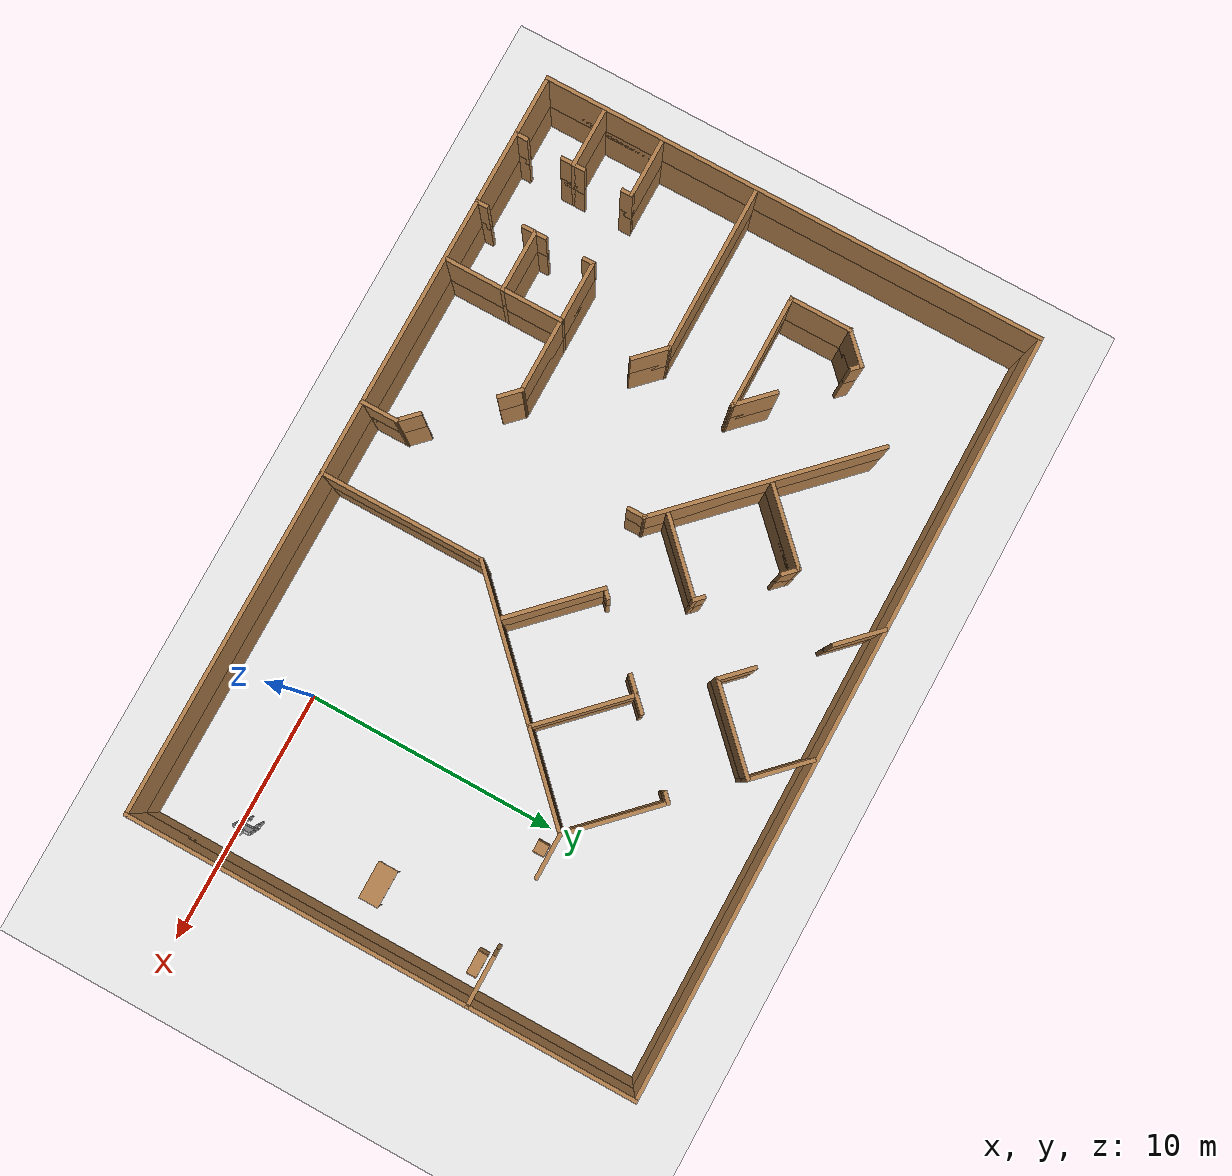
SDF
<sdf version="1.7">
 <world name="default">
  <light name="sun" type="directional">
   <pose>0 0 10 0 -0 0</pose>
   <diffuse>0.8 0.8 0.8 1</diffuse>
   <specular>0.2 0.2 0.2 1</specular>
   <attenuation>
    <range>1000</range>
    <constant>0.9</constant>
    <linear>0.01</linear>
    <quadratic>0.001</quadratic>
   </attenuation>
   <direction>-0.5 0.1 -0.9</direction>
   <spot><inner_angle>0</inner_angle><outer_angle>0</outer_angle><falloff>0</falloff></spot>
  </light>
  <model name="ground_plane">
   <static>1</static>
   <link name="link">
    <collision name="collision">
     <geometry><plane><normal>0 0 1</normal><size>100 100</size></plane></geometry>
     <surface>
      <contact><collide_bitmask>65535</collide_bitmask></contact>
      <friction><ode><mu>100</mu><mu2>50</mu2></ode></friction>
     </surface>
    </collision>
    <visual name="visual">
     <cast_shadows>0</cast_shadows>
     <geometry><plane><normal>0 0 1</normal><size>100 100</size></plane></geometry>
     <material>
      <script><uri>file://media/materials/scripts/gazebo.material</uri><name>Gazebo/White</name></script>
     </material>
    </visual>
   </link>
  </model>
  <gravity>0 0 -9.8</gravity>
  <magnetic_field>6e-06 2.3e-05 -4.2e-05</magnetic_field>
  <atmosphere type="adiabatic"/>
  <scene><ambient>0.4 0.4 0.4 1</ambient><background>0.7 0.7 0.7 1</background><shadows>1</shadows></scene>
  <spherical_coordinates>
   <surface_model>EARTH_WGS84</surface_model>
   <latitude_deg>0</latitude_deg>
   <longitude_deg>0</longitude_deg>
   <elevation>0</elevation>
   <heading_deg>0</heading_deg>
  </spherical_coordinates>
  <physics name="default_physics" default="0" type="ode">
   <ode>
    <solver>
     <type>quick</type>
     <iters>20</iters>
     <sor>1.3</sor>
     <use_dynamic_moi_rescaling>0</use_dynamic_moi_rescaling>
    </solver>
    <constraints>
     <cfm>0</cfm>
     <erp>0.2</erp>
     <contact_max_correcting_vel>100</contact_max_correcting_vel>
     <contact_surface_layer>0.001</contact_surface_layer>
    </constraints>
   </ode>
   <max_step_size>0.002</max_step_size>
   <real_time_factor>1</real_time_factor>
   <real_time_update_rate>500</real_time_update_rate>
  </physics>
  <audio><device>default</device></audio>
  <model name="office_02_clone">
   <pose>-8.5 7 2 0 -0 0</pose>
   <link name="Wall_102">
    <collision name="Wall_102_Collision">
     <geometry><box><size>1.5 0.15 2.5</size></box></geometry>
     <pose>0 0 1.25 0 -0 0</pose>
    </collision>
    <visual name="Wall_102_Visual">
     <pose>0 0 1.25 0 -0 0</pose>
     <geometry><box><size>1.5 0.15 2.5</size></box></geometry>
     <material>
      <script><uri>file://media/materials/scripts/gazebo.material</uri><name>Gazebo/Wood</name></script>
      <ambient>1 1 1 1</ambient>
     </material>
    </visual>
    <pose>2.91922 3.4043 0 0 0 -2.35619</pose>
   </link>
   <link name="Wall_107">
    <collision name="Wall_107_Collision">
     <geometry><box><size>4 0.15 2.5</size></box></geometry>
     <pose>0 0 1.25 0 -0 0</pose>
    </collision>
    <visual name="Wall_107_Visual">
     <pose>0 0 1.25 0 -0 0</pose>
     <geometry><box><size>4 0.15 2.5</size></box></geometry>
     <material>
      <script><uri>file://media/materials/scripts/gazebo.material</uri><name>Gazebo/Wood</name></script>
      <ambient>1 1 1 1</ambient>
     </material>
    </visual>
    <pose>1.57572 -0.661562 0 0 0 -0.785398</pose>
   </link>
   <link name="Wall_109">
    <collision name="Wall_109_Collision">
     <geometry><box><size>3.75 0.15 2.5</size></box></geometry>
     <pose>0 0 1.25 0 -0 0</pose>
    </collision>
    <visual name="Wall_109_Visual">
     <pose>0 0 1.25 0 -0 0</pose>
     <geometry><box><size>3.75 0.15 2.5</size></box></geometry>
     <material>
      <script><uri>file://media/materials/scripts/gazebo.material</uri><name>Gazebo/Wood</name></script>
      <ambient>1 1 1 1</ambient>
     </material>
    </visual>
    <pose>2.37121 6.8868 0 0 0 -2.35619</pose>
   </link>
   <link name="Wall_110">
    <collision name="Wall_110_Collision">
     <geometry><box><size>1.5 0.15 2.5</size></box></geometry>
     <pose>0 0 1.25 0 -0 0</pose>
    </collision>
    <visual name="Wall_110_Visual">
     <pose>0 0 1.25 0 -0 0</pose>
     <geometry><box><size>1.5 0.15 2.5</size></box></geometry>
     <material>
      <script><uri>file://media/materials/scripts/gazebo.material</uri><name>Gazebo/Wood</name></script>
      <ambient>1 1 1 1</ambient>
     </material>
    </visual>
    <pose>0.621125 6.09131 0 0 -0 2.35619</pose>
   </link>
   <link name="Wall_112">
    <collision name="Wall_112_Collision">
     <geometry><box><size>2 0.15 2.5</size></box></geometry>
     <pose>0 0 1.25 0 -0 0</pose>
    </collision>
    <visual name="Wall_112_Visual">
     <pose>0 0 1.25 0 -0 0</pose>
     <geometry><box><size>2 0.15 2.5</size></box></geometry>
     <material>
      <script><uri>file://media/materials/scripts/gazebo.material</uri><name>Gazebo/Wood</name></script>
      <ambient>1 1 1 1</ambient>
     </material>
    </visual>
    <pose>-2.5255 9.23793 0 0 -0 2.35619</pose>
   </link>
   <link name="Wall_116">
    <collision name="Wall_116_Collision">
     <geometry><box><size>9 0.15 2.5</size></box></geometry>
     <pose>0 0 1.25 0 -0 0</pose>
    </collision>
    <visual name="Wall_116_Visual">
     <pose>0 0 1.25 0 -0 0</pose>
     <geometry><box><size>9 0.15 2.5</size></box></geometry>
     <material>
      <script><uri>file://media/materials/scripts/gazebo.material</uri><name>Gazebo/Wood</name></script>
      <ambient>1 1 1 1</ambient>
     </material>
    </visual>
    <pose>-5.76441 3.82857 0 0 -0 2.35619</pose>
   </link>
   <link name="Wall_121">
    <collision name="Wall_121_Collision">
     <geometry><box><size>0.75 0.15 2.5</size></box></geometry>
     <pose>0 0 1.25 0 -0 0</pose>
    </collision>
    <visual name="Wall_121_Visual">
     <pose>0 0 1.25 0 -0 0</pose>
     <geometry><box><size>0.75 0.15 2.5</size></box></geometry>
     <material>
      <script><uri>file://media/materials/scripts/gazebo.material</uri><name>Gazebo/Wood</name></script>
      <ambient>1 1 1 1</ambient>
     </material>
    </visual>
    <pose>-2.63546 0.399619 0 0 0 -1.5708</pose>
   </link>
   <link name="Wall_126">
    <collision name="Wall_126_Collision">
     <geometry><box><size>3.25 0.15 2.5</size></box></geometry>
     <pose>0 0 1.25 0 -0 0</pose>
    </collision>
    <visual name="Wall_126_Visual">
     <pose>0 0 1.25 0 -0 0</pose>
     <geometry><box><size>3.25 0.15 2.5</size></box></geometry>
     <material>
      <script><uri>file://media/materials/scripts/gazebo.material</uri><name>Gazebo/Wood</name></script>
      <ambient>1 1 1 1</ambient>
     </material>
    </visual>
    <pose>-2.01285 2.50274 0 0 0 -2.35619</pose>
   </link>
   <link name="Wall_131">
    <collision name="Wall_131_Collision">
     <geometry><box><size>0.5 0.15 2.5</size></box></geometry>
     <pose>0 0 1.25 0 -0 0</pose>
    </collision>
    <visual name="Wall_131_Visual">
     <pose>0 0 1.25 0 -0 0</pose>
     <geometry><box><size>0.5 0.15 2.5</size></box></geometry>
     <material>
      <script><uri>file://media/materials/scripts/gazebo.material</uri><name>Gazebo/Wood</name></script>
      <ambient>1 1 1 1</ambient>
     </material>
    </visual>
    <pose>-1.04058 3.7225 0 0 -0 2.35619</pose>
   </link>
   <link name="Wall_134">
    <collision name="Wall_134_Collision">
     <geometry><box><size>0.75 0.15 2.5</size></box></geometry>
     <pose>0 0 1.25 0 -0 0</pose>
    </collision>
    <visual name="Wall_134_Visual">
     <pose>0 0 1.25 0 -0 0</pose>
     <geometry><box><size>0.75 0.15 2.5</size></box></geometry>
     <material>
      <script><uri>file://media/materials/scripts/gazebo.material</uri><name>Gazebo/Wood</name></script>
      <ambient>1 1 1 1</ambient>
     </material>
    </visual>
    <pose>-3.39171 6.07363 0 0 -0 2.35619</pose>
   </link>
   <link name="Wall_135">
    <collision name="Wall_135_Collision">
     <geometry><box><size>3.25 0.15 2.5</size></box></geometry>
     <pose>0 0 1.25 0 -0 0</pose>
    </collision>
    <visual name="Wall_135_Visual">
     <pose>0 0 1.25 0 -0 0</pose>
     <geometry><box><size>3.25 0.15 2.5</size></box></geometry>
     <material>
      <script><uri>file://media/materials/scripts/gazebo.material</uri><name>Gazebo/Wood</name></script>
      <ambient>1 1 1 1</ambient>
     </material>
    </visual>
    <pose>-4.69985 5.18975 0 0 0 -2.35619</pose>
   </link>
   <link name="Wall_160">
    <collision name="Wall_160_Collision">
     <geometry><box><size>2.5 0.15 2.5</size></box></geometry>
     <pose>0 0 1.25 0 -0 0</pose>
    </collision>
    <visual name="Wall_160_Visual">
     <pose>0 0 1.25 0 -0 0</pose>
     <geometry><box><size>2.5 0.15 2.5</size></box></geometry>
     <material>
      <script><uri>file://media/materials/scripts/gazebo.material</uri><name>Gazebo/Wood</name></script>
      <ambient>1 1 1 1</ambient>
     </material>
    </visual>
    <pose>-13.7509 -7.575 0 0 -0 0</pose>
   </link>
   <link name="Wall_164">
    <collision name="Wall_164_Collision">
     <geometry><box><size>2.5 0.15 2.5</size></box></geometry>
     <pose>0 0 1.25 0 -0 0</pose>
    </collision>
    <visual name="Wall_164_Visual">
     <pose>0 0 1.25 0 -0 0</pose>
     <geometry><box><size>2.5 0.15 2.5</size></box></geometry>
     <material>
      <script><uri>file://media/materials/scripts/gazebo.material</uri><name>Gazebo/Wood</name></script>
      <ambient>1 1 1 1</ambient>
     </material>
    </visual>
    <pose>-13.7509 -5.225 0 0 -0 0</pose>
   </link>
   <link name="Wall_171">
    <collision name="Wall_171_Collision">
     <geometry><box><size>2.5 0.15 2.5</size></box></geometry>
     <pose>0 0 1.25 0 -0 0</pose>
    </collision>
    <visual name="Wall_171_Visual">
     <pose>0 0 1.25 0 -0 0</pose>
     <geometry><box><size>2.5 0.15 2.5</size></box></geometry>
     <material>
      <script><uri>file://media/materials/scripts/gazebo.material</uri><name>Gazebo/Wood</name></script>
      <ambient>1 1 1 1</ambient>
     </material>
    </visual>
    <pose>-8.55093 -7.575 0 0 -0 0</pose>
   </link>
   <link name="Wall_173">
    <collision name="Wall_173_Collision">
     <geometry><box><size>0.5 0.15 2.5</size></box></geometry>
     <pose>0 0 1.25 0 -0 0</pose>
    </collision>
    <visual name="Wall_173_Visual">
     <pose>0 0 1.25 0 -0 0</pose>
     <geometry><box><size>0.5 0.15 2.5</size></box></geometry>
     <material>
      <script><uri>file://media/materials/scripts/gazebo.material</uri><name>Gazebo/Wood</name></script>
      <ambient>1 1 1 1</ambient>
     </material>
    </visual>
    <pose>-12.5759 -5.4 0 0 0 -1.5708</pose>
   </link>
   <link name="Wall_175">
    <collision name="Wall_175_Collision">
     <geometry><box><size>0.5 0.15 2.5</size></box></geometry>
     <pose>0 0 1.25 0 -0 0</pose>
    </collision>
    <visual name="Wall_175_Visual">
     <pose>0 0 1.25 0 -0 0</pose>
     <geometry><box><size>0.5 0.15 2.5</size></box></geometry>
     <material>
      <script><uri>file://media/materials/scripts/gazebo.material</uri><name>Gazebo/Wood</name></script>
      <ambient>1 1 1 1</ambient>
     </material>
    </visual>
    <pose>-9.72593 -5.4 0 0 0 -1.5708</pose>
   </link>
   <link name="Wall_178">
    <collision name="Wall_178_Collision">
     <geometry><box><size>1 0.15 2.5</size></box></geometry>
     <pose>0 0 1.25 0 -0 0</pose>
    </collision>
    <visual name="Wall_178_Visual">
     <pose>0 0 1.25 0 -0 0</pose>
     <geometry><box><size>1 0.15 2.5</size></box></geometry>
     <material>
      <script><uri>file://media/materials/scripts/gazebo.material</uri><name>Gazebo/Wood</name></script>
      <ambient>1 1 1 1</ambient>
     </material>
    </visual>
    <pose>-12.5759 -7.6 0 0 0 -1.5708</pose>
   </link>
   <link name="Wall_183">
    <collision name="Wall_183_Collision">
     <geometry><box><size>0.5 0.15 2.5</size></box></geometry>
     <pose>0 0 1.25 0 -0 0</pose>
    </collision>
    <visual name="Wall_183_Visual">
     <pose>0 0 1.25 0 -0 0</pose>
     <geometry><box><size>0.5 0.15 2.5</size></box></geometry>
     <material>
      <script><uri>file://media/materials/scripts/gazebo.material</uri><name>Gazebo/Wood</name></script>
      <ambient>1 1 1 1</ambient>
     </material>
    </visual>
    <pose>-12.5759 -9.685 0 0 0 -1.5708</pose>
   </link>
   <link name="Wall_186">
    <collision name="Wall_186_Collision">
     <geometry><box><size>1 0.15 2.5</size></box></geometry>
     <pose>0 0 1.25 0 -0 0</pose>
    </collision>
    <visual name="Wall_186_Visual">
     <pose>0 0 1.25 0 -0 0</pose>
     <geometry><box><size>1 0.15 2.5</size></box></geometry>
     <material>
      <script><uri>file://media/materials/scripts/gazebo.material</uri><name>Gazebo/Wood</name></script>
      <ambient>1 1 1 1</ambient>
     </material>
    </visual>
    <pose>-9.72593 -7.6 0 0 0 -1.5708</pose>
   </link>
   <link name="Wall_188">
    <collision name="Wall_188_Collision">
     <geometry><box><size>0.5 0.15 2.5</size></box></geometry>
     <pose>0 0 1.25 0 -0 0</pose>
    </collision>
    <visual name="Wall_188_Visual">
     <pose>0 0 1.25 0 -0 0</pose>
     <geometry><box><size>0.5 0.15 2.5</size></box></geometry>
     <material>
      <script><uri>file://media/materials/scripts/gazebo.material</uri><name>Gazebo/Wood</name></script>
      <ambient>1 1 1 1</ambient>
     </material>
    </visual>
    <pose>-9.72593 -9.731 0 0 0 -1.5708</pose>
   </link>
   <link name="Wall_194">
    <collision name="Wall_194_Collision">
     <geometry><box><size>1.5 0.15 2.5</size></box></geometry>
     <pose>0 0 1.25 0 -0 0</pose>
    </collision>
    <visual name="Wall_194_Visual">
     <pose>0 0 1.25 0 -0 0</pose>
     <geometry><box><size>1.5 0.15 2.5</size></box></geometry>
     <material>
      <script><uri>file://media/materials/scripts/gazebo.material</uri><name>Gazebo/Wood</name></script>
      <ambient>1 1 1 1</ambient>
     </material>
    </visual>
    <pose>-7.85323 -1.8977 0 0 -0 2.35619</pose>
   </link>
   <link name="Wall_195">
    <collision name="Wall_195_Collision">
     <geometry><box><size>6.75 0.15 2.5</size></box></geometry>
     <pose>0 0 1.25 0 -0 0</pose>
    </collision>
    <visual name="Wall_195_Visual">
     <pose>0 0 1.25 0 -0 0</pose>
     <geometry><box><size>6.75 0.15 2.5</size></box></geometry>
     <material>
      <script><uri>file://media/materials/scripts/gazebo.material</uri><name>Gazebo/Wood</name></script>
      <ambient>1 1 1 1</ambient>
     </material>
    </visual>
    <pose>-11.6305 -1.42041 0 0 -0 3.14159</pose>
   </link>
   <link name="Wall_200">
    <collision name="Wall_200_Collision">
     <geometry><box><size>1.5 0.15 2.5</size></box></geometry>
     <pose>0 0 1.25 0 -0 0</pose>
    </collision>
    <visual name="Wall_200_Visual">
     <pose>0 0 1.25 0 -0 0</pose>
     <geometry><box><size>1.5 0.15 2.5</size></box></geometry>
     <material>
      <script><uri>file://media/materials/scripts/gazebo.material</uri><name>Gazebo/Wood</name></script>
      <ambient>1 1 1 1</ambient>
     </material>
    </visual>
    <pose>-1.45644 -9.23222 0 0 -0 1.5708</pose>
   </link>
   <link name="Wall_229">
    <collision name="Wall_229_Collision">
     <geometry><box><size>4.5 0.15 2.5</size></box></geometry>
     <pose>0 0 1.25 0 -0 0</pose>
    </collision>
    <visual name="Wall_229_Visual">
     <pose>0 0 1.25 0 -0 0</pose>
     <geometry><box><size>4.5 0.15 2.5</size></box></geometry>
     <material>
      <script><uri>file://media/materials/scripts/gazebo.material</uri><name>Gazebo/Wood</name></script>
      <ambient>1 1 1 1</ambient>
     </material>
    </visual>
    <pose>-9.79935 1.52745 0 0 -0 0</pose>
   </link>
   <link name="Wall_230">
    <collision name="Wall_230_Collision">
     <geometry><box><size>1.75 0.15 2.5</size></box></geometry>
     <pose>0 0 1.25 0 -0 0</pose>
    </collision>
    <visual name="Wall_230_Visual">
     <pose>0 0 1.25 0 -0 0</pose>
     <geometry><box><size>1.75 0.15 2.5</size></box></geometry>
     <material>
      <script><uri>file://media/materials/scripts/gazebo.material</uri><name>Gazebo/Wood</name></script>
      <ambient>1 1 1 1</ambient>
     </material>
    </visual>
    <pose>-8.19003 2.09313 0 0 -0 2.35619</pose>
   </link>
   <link name="Wall_244">
    <collision name="Wall_244_Collision">
     <geometry><box><size>2.5 0.15 2.5</size></box></geometry>
     <pose>0 0 1.25 0 -0 0</pose>
    </collision>
    <visual name="Wall_244_Visual">
     <pose>0 0 1.25 0 -0 0</pose>
     <geometry><box><size>2.5 0.15 2.5</size></box></geometry>
     <material>
      <script><uri>file://media/materials/scripts/gazebo.material</uri><name>Gazebo/Wood</name></script>
      <ambient>1 1 1 1</ambient>
     </material>
    </visual>
    <pose>-11.9743 2.70245 0 0 -0 1.5708</pose>
   </link>
   <link name="Wall_246">
    <collision name="Wall_246_Collision">
     <geometry><box><size>1.5 0.15 2.5</size></box></geometry>
     <pose>0 0 1.25 0 -0 0</pose>
    </collision>
    <visual name="Wall_246_Visual">
     <pose>0 0 1.25 0 -0 0</pose>
     <geometry><box><size>1.5 0.15 2.5</size></box></geometry>
     <material>
      <script><uri>file://media/materials/scripts/gazebo.material</uri><name>Gazebo/Wood</name></script>
      <ambient>1 1 1 1</ambient>
     </material>
    </visual>
    <pose>-11.4971 4.35474 0 0 -0 0.785398</pose>
   </link>
   <link name="Wall_247">
    <collision name="Wall_247_Collision">
     <geometry><box><size>0.5 0.15 2.5</size></box></geometry>
     <pose>0 0 1.25 0 -0 0</pose>
    </collision>
    <visual name="Wall_247_Visual">
     <pose>0 0 1.25 0 -0 0</pose>
     <geometry><box><size>0.5 0.15 2.5</size></box></geometry>
     <material>
      <script><uri>file://media/materials/scripts/gazebo.material</uri><name>Gazebo/Wood</name></script>
      <ambient>1 1 1 1</ambient>
     </material>
    </visual>
    <pose>-10.896 4.7083 0 0 0 -0.785398</pose>
   </link>
   <link name="Wall_253">
    <collision name="Wall_253_Collision">
     <geometry><box><size>2.5 0.15 2.5</size></box></geometry>
     <pose>0 0 1.25 0 -0 0</pose>
    </collision>
    <visual name="Wall_253_Visual">
     <pose>0 0 1.25 0 -0 0</pose>
     <geometry><box><size>2.5 0.15 2.5</size></box></geometry>
     <material>
      <script><uri>file://media/materials/scripts/gazebo.material</uri><name>Gazebo/Wood</name></script>
      <ambient>1 1 1 1</ambient>
     </material>
    </visual>
    <pose>-8.55093 -5.225 0 0 -0 0</pose>
   </link>
   <link name="Wall_254">
    <collision name="Wall_254_Collision">
     <geometry><box><size>4.75 0.15 2.5</size></box></geometry>
     <pose>0 0 1.25 0 -0 0</pose>
    </collision>
    <visual name="Wall_254_Visual">
     <pose>0 0 1.25 0 -0 0</pose>
     <geometry><box><size>4.75 0.15 2.5</size></box></geometry>
     <material>
      <script><uri>file://media/materials/scripts/gazebo.material</uri><name>Gazebo/Wood</name></script>
      <ambient>1 1 1 1</ambient>
     </material>
    </visual>
    <pose>-7.37593 -7.525 0 0 0 -1.5708</pose>
   </link>
   <link name="Wall_258">
    <collision name="Wall_258_Collision">
     <geometry><box><size>3 0.15 2.5</size></box></geometry>
     <pose>0 0 1.25 0 -0 0</pose>
    </collision>
    <visual name="Wall_258_Visual">
     <pose>0 0 1.25 0 -0 0</pose>
     <geometry><box><size>3 0.15 2.5</size></box></geometry>
     <material>
      <script><uri>file://media/materials/scripts/gazebo.material</uri><name>Gazebo/Wood</name></script>
      <ambient>1 1 1 1</ambient>
     </material>
    </visual>
    <pose>-5.95093 -5.225 0 0 -0 0</pose>
   </link>
   <link name="Wall_259">
    <collision name="Wall_259_Collision">
     <geometry><box><size>1 0.15 2.5</size></box></geometry>
     <pose>0 0 1.25 0 -0 0</pose>
    </collision>
    <visual name="Wall_259_Visual">
     <pose>0 0 1.25 0 -0 0</pose>
     <geometry><box><size>1 0.15 2.5</size></box></geometry>
     <material>
      <script><uri>file://media/materials/scripts/gazebo.material</uri><name>Gazebo/Wood</name></script>
      <ambient>1 1 1 1</ambient>
     </material>
    </visual>
    <pose>-4.22541 -5.52552 0 0 0 -0.785398</pose>
   </link>
   <link name="Wall_261">
    <collision name="Wall_261_Collision">
     <geometry><box><size>1 0.15 2.5</size></box></geometry>
     <pose>0 0 1.25 0 -0 0</pose>
    </collision>
    <visual name="Wall_261_Visual">
     <pose>0 0 1.25 0 -0 0</pose>
     <geometry><box><size>1 0.15 2.5</size></box></geometry>
     <material>
      <script><uri>file://media/materials/scripts/gazebo.material</uri><name>Gazebo/Wood</name></script>
      <ambient>1 1 1 1</ambient>
     </material>
    </visual>
    <pose>-1.75697 -8.2567 0 0 -0 2.35619</pose>
   </link>
   <link name="Wall_5">
    <collision name="Wall_5_Collision">
     <geometry><box><size>20 0.15 2.5</size></box></geometry>
     <pose>0 0 1.25 0 -0 0</pose>
    </collision>
    <visual name="Wall_5_Visual">
     <pose>0 0 1.25 0 -0 0</pose>
     <geometry><box><size>20 0.15 2.5</size></box></geometry>
     <material>
      <script><uri>file://media/materials/scripts/gazebo.material</uri><name>Gazebo/Wood</name></script>
      <ambient>1 1 1 1</ambient>
     </material>
    </visual>
    <pose>-14.9259 0 0 0 0 -1.5708</pose>
   </link>
   <link name="Wall_51">
    <collision name="Wall_51_Collision">
     <geometry><box><size>6.5 0.15 2.5</size></box></geometry>
     <pose>0 0 1.25 0 -0 0</pose>
    </collision>
    <visual name="Wall_51_Visual">
     <pose>0 0 1.25 0 -0 0</pose>
     <geometry><box><size>6.5 0.15 2.5</size></box></geometry>
     <material>
      <script><uri>file://media/materials/scripts/gazebo.material</uri><name>Gazebo/Wood</name></script>
      <ambient>1 1 1 1</ambient>
     </material>
    </visual>
    <pose>1.41662 -6.71802 0 0 -0 1.5708</pose>
   </link>
   <link name="Wall_55">
    <collision name="Wall_55_Collision">
     <geometry><box><size>10 0.15 2.5</size></box></geometry>
     <pose>0 0 1.25 0 -0 0</pose>
    </collision>
    <visual name="Wall_55_Visual">
     <pose>0 0 1.25 0 -0 0</pose>
     <geometry><box><size>10 0.15 2.5</size></box></geometry>
     <material>
      <script><uri>file://media/materials/scripts/gazebo.material</uri><name>Gazebo/Wood</name></script>
      <ambient>1 1 1 1</ambient>
     </material>
    </visual>
    <pose>4.89912 -0.060521 0 0 0 -2.35619</pose>
   </link>
   <link name="Wall_57">
    <collision name="Wall_57_Collision">
     <geometry><box><size>1.8029 0.15 2.5</size></box></geometry>
     <pose>0 0 1.25 0 -0 0</pose>
    </collision>
    <visual name="Wall_57_Visual">
     <pose>0 0 1.25 0 -0 0</pose>
     <geometry><box><size>1.8029 0.15 2.5</size></box></geometry>
     <material>
      <script><uri>file://media/materials/scripts/gazebo.material</uri><name>Gazebo/Wood</name></script>
      <ambient>1 1 1 1</ambient>
     </material>
    </visual>
    <pose>9.20807 3.42198 0 0 -0 0</pose>
   </link>
   <link name="Wall_59">
    <collision name="Wall_59_Collision">
     <geometry><box><size>2 0.15 2.5</size></box></geometry>
     <pose>0 0 1.25 0 -0 0</pose>
    </collision>
    <visual name="Wall_59_Visual">
     <pose>0 0 1.25 0 -0 0</pose>
     <geometry><box><size>2 0.15 2.5</size></box></geometry>
     <material>
      <script><uri>file://media/materials/scripts/gazebo.material</uri><name>Gazebo/Wood</name></script>
      <ambient>1 1 1 1</ambient>
     </material>
    </visual>
    <pose>14.0055 3.43241 0 0 -0 3.14159</pose>
   </link>
   <link name="Wall_6">
    <collision name="Wall_6_Collision">
     <geometry><box><size>30 0.15 2.5</size></box></geometry>
     <pose>0 0 1.25 0 -0 0</pose>
    </collision>
    <visual name="Wall_6_Visual">
     <pose>0 0 1.25 0 -0 0</pose>
     <geometry><box><size>30 0.15 2.5</size></box></geometry>
     <material>
      <script><uri>file://media/materials/scripts/gazebo.material</uri><name>Gazebo/Wood</name></script>
      <ambient>1 1 1 1</ambient>
     </material>
    </visual>
    <pose>-0.000934 -9.925 0 0 -0 0</pose>
   </link>
   <link name="Wall_7">
    <collision name="Wall_7_Collision">
     <geometry><box><size>20 0.15 2.5</size></box></geometry>
     <pose>0 0 1.25 0 -0 0</pose>
    </collision>
    <visual name="Wall_7_Visual">
     <pose>0 0 1.25 0 -0 0</pose>
     <geometry><box><size>20 0.15 2.5</size></box></geometry>
     <material>
      <script><uri>file://media/materials/scripts/gazebo.material</uri><name>Gazebo/Wood</name></script>
      <ambient>1 1 1 1</ambient>
     </material>
    </visual>
    <pose>14.9241 0 0 0 -0 1.5708</pose>
   </link>
   <link name="Wall_8">
    <collision name="Wall_8_Collision">
     <geometry><box><size>30 0.15 2.5</size></box></geometry>
     <pose>0 0 1.25 0 -0 0</pose>
    </collision>
    <visual name="Wall_8_Visual">
     <pose>0 0 1.25 0 -0 0</pose>
     <geometry><box><size>30 0.15 2.5</size></box></geometry>
     <material>
      <script><uri>file://media/materials/scripts/gazebo.material</uri><name>Gazebo/Wood</name></script>
      <ambient>1 1 1 1</ambient>
     </material>
    </visual>
    <pose>-0.000934 9.925 0 0 -0 3.14159</pose>
   </link>
   <link name="Wall_80">
    <collision name="Wall_80_Collision">
     <geometry><box><size>4 0.15 2.5</size></box></geometry>
     <pose>0 0 1.25 0 -0 0</pose>
    </collision>
    <visual name="Wall_80_Visual">
     <pose>0 0 1.25 0 -0 0</pose>
     <geometry><box><size>4 0.15 2.5</size></box></geometry>
     <material>
      <script><uri>file://media/materials/scripts/gazebo.material</uri><name>Gazebo/Wood</name></script>
      <ambient>1 1 1 1</ambient>
     </material>
    </visual>
    <pose>7.02044 4.78316 0 0 -0 2.35619</pose>
   </link>
   <link name="Wall_82">
    <collision name="Wall_82_Collision">
     <geometry><box><size>2.5 0.15 2.5</size></box></geometry>
     <pose>0 0 1.25 0 -0 0</pose>
    </collision>
    <visual name="Wall_82_Visual">
     <pose>0 0 1.25 0 -0 0</pose>
     <geometry><box><size>2.5 0.15 2.5</size></box></geometry>
     <material>
      <script><uri>file://media/materials/scripts/gazebo.material</uri><name>Gazebo/Wood</name></script>
      <ambient>1 1 1 1</ambient>
     </material>
    </visual>
    <pose>2.81316 8.99044 0 0 -0 2.35619</pose>
   </link>
   <link name="Wall_87">
    <collision name="Wall_87_Collision">
     <geometry><box><size>4 0.15 2.5</size></box></geometry>
     <pose>0 0 1.25 0 -0 0</pose>
    </collision>
    <visual name="Wall_87_Visual">
     <pose>0 0 1.25 0 -0 0</pose>
     <geometry><box><size>4 0.15 2.5</size></box></geometry>
     <material>
      <script><uri>file://media/materials/scripts/gazebo.material</uri><name>Gazebo/Wood</name></script>
      <ambient>1 1 1 1</ambient>
     </material>
    </visual>
    <pose>4.29808 2.0608 0 0 -0 2.35619</pose>
   </link>
   <link name="Wall_90">
    <collision name="Wall_90_Collision">
     <geometry><box><size>0.5 0.15 2.5</size></box></geometry>
     <pose>0 0 1.25 0 -0 0</pose>
    </collision>
    <visual name="Wall_90_Visual">
     <pose>0 0 1.25 0 -0 0</pose>
     <geometry><box><size>0.5 0.15 2.5</size></box></geometry>
     <material>
      <script><uri>file://media/materials/scripts/gazebo.material</uri><name>Gazebo/Wood</name></script>
      <ambient>1 1 1 1</ambient>
     </material>
    </visual>
    <pose>5.53552 6.0206 0 0 0 -2.35619</pose>
   </link>
   <link name="Wall_94">
    <collision name="Wall_94_Collision">
     <geometry><box><size>0.5 0.15 2.5</size></box></geometry>
     <pose>0 0 1.25 0 -0 0</pose>
    </collision>
    <visual name="Wall_94_Visual">
     <pose>0 0 1.25 0 -0 0</pose>
     <geometry><box><size>0.5 0.15 2.5</size></box></geometry>
     <material>
      <script><uri>file://media/materials/scripts/gazebo.material</uri><name>Gazebo/Wood</name></script>
      <ambient>1 1 1 1</ambient>
     </material>
    </visual>
    <pose>0.338283 0.823362 0 0 -0 0.785398</pose>
   </link>
   <static>1</static>
  </model>
  <model name="office_02_clone_clone">
   <pose>-8.5 7 0 0 -0 0</pose>
   <link name="Wall_102">
    <collision name="Wall_102_Collision">
     <geometry><box><size>1.5 0.15 2.5</size></box></geometry>
     <pose>0 0 1.25 0 -0 0</pose>
    </collision>
    <visual name="Wall_102_Visual">
     <pose>0 0 1.25 0 -0 0</pose>
     <geometry><box><size>1.5 0.15 2.5</size></box></geometry>
     <material>
      <script><uri>file://media/materials/scripts/gazebo.material</uri><name>Gazebo/Wood</name></script>
      <ambient>1 1 1 1</ambient>
     </material>
    </visual>
    <pose>2.91922 3.4043 0 0 0 -2.35619</pose>
   </link>
   <link name="Wall_107">
    <collision name="Wall_107_Collision">
     <geometry><box><size>4 0.15 2.5</size></box></geometry>
     <pose>0 0 1.25 0 -0 0</pose>
    </collision>
    <visual name="Wall_107_Visual">
     <pose>0 0 1.25 0 -0 0</pose>
     <geometry><box><size>4 0.15 2.5</size></box></geometry>
     <material>
      <script><uri>file://media/materials/scripts/gazebo.material</uri><name>Gazebo/Wood</name></script>
      <ambient>1 1 1 1</ambient>
     </material>
    </visual>
    <pose>1.57572 -0.661562 0 0 0 -0.785398</pose>
   </link>
   <link name="Wall_109">
    <collision name="Wall_109_Collision">
     <geometry><box><size>3.75 0.15 2.5</size></box></geometry>
     <pose>0 0 1.25 0 -0 0</pose>
    </collision>
    <visual name="Wall_109_Visual">
     <pose>0 0 1.25 0 -0 0</pose>
     <geometry><box><size>3.75 0.15 2.5</size></box></geometry>
     <material>
      <script><uri>file://media/materials/scripts/gazebo.material</uri><name>Gazebo/Wood</name></script>
      <ambient>1 1 1 1</ambient>
     </material>
    </visual>
    <pose>2.37121 6.8868 0 0 0 -2.35619</pose>
   </link>
   <link name="Wall_110">
    <collision name="Wall_110_Collision">
     <geometry><box><size>1.5 0.15 2.5</size></box></geometry>
     <pose>0 0 1.25 0 -0 0</pose>
    </collision>
    <visual name="Wall_110_Visual">
     <pose>0 0 1.25 0 -0 0</pose>
     <geometry><box><size>1.5 0.15 2.5</size></box></geometry>
     <material>
      <script><uri>file://media/materials/scripts/gazebo.material</uri><name>Gazebo/Wood</name></script>
      <ambient>1 1 1 1</ambient>
     </material>
    </visual>
    <pose>0.621125 6.09131 0 0 -0 2.35619</pose>
   </link>
   <link name="Wall_112">
    <collision name="Wall_112_Collision">
     <geometry><box><size>2 0.15 2.5</size></box></geometry>
     <pose>0 0 1.25 0 -0 0</pose>
    </collision>
    <visual name="Wall_112_Visual">
     <pose>0 0 1.25 0 -0 0</pose>
     <geometry><box><size>2 0.15 2.5</size></box></geometry>
     <material>
      <script><uri>file://media/materials/scripts/gazebo.material</uri><name>Gazebo/Wood</name></script>
      <ambient>1 1 1 1</ambient>
     </material>
    </visual>
    <pose>-2.5255 9.23793 0 0 -0 2.35619</pose>
   </link>
   <link name="Wall_116">
    <collision name="Wall_116_Collision">
     <geometry><box><size>9 0.15 2.5</size></box></geometry>
     <pose>0 0 1.25 0 -0 0</pose>
    </collision>
    <visual name="Wall_116_Visual">
     <pose>0 0 1.25 0 -0 0</pose>
     <geometry><box><size>9 0.15 2.5</size></box></geometry>
     <material>
      <script><uri>file://media/materials/scripts/gazebo.material</uri><name>Gazebo/Wood</name></script>
      <ambient>1 1 1 1</ambient>
     </material>
    </visual>
    <pose>-5.76441 3.82857 0 0 -0 2.35619</pose>
   </link>
   <link name="Wall_121">
    <collision name="Wall_121_Collision">
     <geometry><box><size>0.75 0.15 2.5</size></box></geometry>
     <pose>0 0 1.25 0 -0 0</pose>
    </collision>
    <visual name="Wall_121_Visual">
     <pose>0 0 1.25 0 -0 0</pose>
     <geometry><box><size>0.75 0.15 2.5</size></box></geometry>
     <material>
      <script><uri>file://media/materials/scripts/gazebo.material</uri><name>Gazebo/Wood</name></script>
      <ambient>1 1 1 1</ambient>
     </material>
    </visual>
    <pose>-2.63546 0.399619 0 0 0 -1.5708</pose>
   </link>
   <link name="Wall_126">
    <collision name="Wall_126_Collision">
     <geometry><box><size>3.25 0.15 2.5</size></box></geometry>
     <pose>0 0 1.25 0 -0 0</pose>
    </collision>
    <visual name="Wall_126_Visual">
     <pose>0 0 1.25 0 -0 0</pose>
     <geometry><box><size>3.25 0.15 2.5</size></box></geometry>
     <material>
      <script><uri>file://media/materials/scripts/gazebo.material</uri><name>Gazebo/Wood</name></script>
      <ambient>1 1 1 1</ambient>
     </material>
    </visual>
    <pose>-2.01285 2.50274 0 0 0 -2.35619</pose>
   </link>
   <link name="Wall_131">
    <collision name="Wall_131_Collision">
     <geometry><box><size>0.5 0.15 2.5</size></box></geometry>
     <pose>0 0 1.25 0 -0 0</pose>
    </collision>
    <visual name="Wall_131_Visual">
     <pose>0 0 1.25 0 -0 0</pose>
     <geometry><box><size>0.5 0.15 2.5</size></box></geometry>
     <material>
      <script><uri>file://media/materials/scripts/gazebo.material</uri><name>Gazebo/Wood</name></script>
      <ambient>1 1 1 1</ambient>
     </material>
    </visual>
    <pose>-1.04058 3.7225 0 0 -0 2.35619</pose>
   </link>
   <link name="Wall_134">
    <collision name="Wall_134_Collision">
     <geometry><box><size>0.75 0.15 2.5</size></box></geometry>
     <pose>0 0 1.25 0 -0 0</pose>
    </collision>
    <visual name="Wall_134_Visual">
     <pose>0 0 1.25 0 -0 0</pose>
     <geometry><box><size>0.75 0.15 2.5</size></box></geometry>
     <material>
      <script><uri>file://media/materials/scripts/gazebo.material</uri><name>Gazebo/Wood</name></script>
      <ambient>1 1 1 1</ambient>
     </material>
    </visual>
    <pose>-3.39171 6.07363 0 0 -0 2.35619</pose>
   </link>
   <link name="Wall_135">
    <collision name="Wall_135_Collision">
     <geometry><box><size>3.25 0.15 2.5</size></box></geometry>
     <pose>0 0 1.25 0 -0 0</pose>
    </collision>
    <visual name="Wall_135_Visual">
     <pose>0 0 1.25 0 -0 0</pose>
     <geometry><box><size>3.25 0.15 2.5</size></box></geometry>
     <material>
      <script><uri>file://media/materials/scripts/gazebo.material</uri><name>Gazebo/Wood</name></script>
      <ambient>1 1 1 1</ambient>
     </material>
    </visual>
    <pose>-4.69985 5.18975 0 0 0 -2.35619</pose>
   </link>
   <link name="Wall_160">
    <collision name="Wall_160_Collision">
     <geometry><box><size>2.5 0.15 2.5</size></box></geometry>
     <pose>0 0 1.25 0 -0 0</pose>
    </collision>
    <visual name="Wall_160_Visual">
     <pose>0 0 1.25 0 -0 0</pose>
     <geometry><box><size>2.5 0.15 2.5</size></box></geometry>
     <material>
      <script><uri>file://media/materials/scripts/gazebo.material</uri><name>Gazebo/Wood</name></script>
      <ambient>1 1 1 1</ambient>
     </material>
    </visual>
    <pose>-13.7509 -7.575 0 0 -0 0</pose>
   </link>
   <link name="Wall_164">
    <collision name="Wall_164_Collision">
     <geometry><box><size>2.5 0.15 2.5</size></box></geometry>
     <pose>0 0 1.25 0 -0 0</pose>
    </collision>
    <visual name="Wall_164_Visual">
     <pose>0 0 1.25 0 -0 0</pose>
     <geometry><box><size>2.5 0.15 2.5</size></box></geometry>
     <material>
      <script><uri>file://media/materials/scripts/gazebo.material</uri><name>Gazebo/Wood</name></script>
      <ambient>1 1 1 1</ambient>
     </material>
    </visual>
    <pose>-13.7509 -5.225 0 0 -0 0</pose>
   </link>
   <link name="Wall_171">
    <collision name="Wall_171_Collision">
     <geometry><box><size>2.5 0.15 2.5</size></box></geometry>
     <pose>0 0 1.25 0 -0 0</pose>
    </collision>
    <visual name="Wall_171_Visual">
     <pose>0 0 1.25 0 -0 0</pose>
     <geometry><box><size>2.5 0.15 2.5</size></box></geometry>
     <material>
      <script><uri>file://media/materials/scripts/gazebo.material</uri><name>Gazebo/Wood</name></script>
      <ambient>1 1 1 1</ambient>
     </material>
    </visual>
    <pose>-8.55093 -7.575 0 0 -0 0</pose>
   </link>
   <link name="Wall_173">
    <collision name="Wall_173_Collision">
     <geometry><box><size>0.5 0.15 2.5</size></box></geometry>
     <pose>0 0 1.25 0 -0 0</pose>
    </collision>
    <visual name="Wall_173_Visual">
     <pose>0 0 1.25 0 -0 0</pose>
     <geometry><box><size>0.5 0.15 2.5</size></box></geometry>
     <material>
      <script><uri>file://media/materials/scripts/gazebo.material</uri><name>Gazebo/Wood</name></script>
      <ambient>1 1 1 1</ambient>
     </material>
    </visual>
    <pose>-12.5759 -5.4 0 0 0 -1.5708</pose>
   </link>
   <link name="Wall_175">
    <collision name="Wall_175_Collision">
     <geometry><box><size>0.5 0.15 2.5</size></box></geometry>
     <pose>0 0 1.25 0 -0 0</pose>
    </collision>
    <visual name="Wall_175_Visual">
     <pose>0 0 1.25 0 -0 0</pose>
     <geometry><box><size>0.5 0.15 2.5</size></box></geometry>
     <material>
      <script><uri>file://media/materials/scripts/gazebo.material</uri><name>Gazebo/Wood</name></script>
      <ambient>1 1 1 1</ambient>
     </material>
    </visual>
    <pose>-9.72593 -5.4 0 0 0 -1.5708</pose>
   </link>
   <link name="Wall_178">
    <collision name="Wall_178_Collision">
     <geometry><box><size>1 0.15 2.5</size></box></geometry>
     <pose>0 0 1.25 0 -0 0</pose>
    </collision>
    <visual name="Wall_178_Visual">
     <pose>0 0 1.25 0 -0 0</pose>
     <geometry><box><size>1 0.15 2.5</size></box></geometry>
     <material>
      <script><uri>file://media/materials/scripts/gazebo.material</uri><name>Gazebo/Wood</name></script>
      <ambient>1 1 1 1</ambient>
     </material>
    </visual>
    <pose>-12.5759 -7.6 0 0 0 -1.5708</pose>
   </link>
   <link name="Wall_183">
    <collision name="Wall_183_Collision">
     <geometry><box><size>0.5 0.15 2.5</size></box></geometry>
     <pose>0 0 1.25 0 -0 0</pose>
    </collision>
    <visual name="Wall_183_Visual">
     <pose>0 0 1.25 0 -0 0</pose>
     <geometry><box><size>0.5 0.15 2.5</size></box></geometry>
     <material>
      <script><uri>file://media/materials/scripts/gazebo.material</uri><name>Gazebo/Wood</name></script>
      <ambient>1 1 1 1</ambient>
     </material>
    </visual>
    <pose>-12.5759 -9.685 0 0 0 -1.5708</pose>
   </link>
   <link name="Wall_186">
    <collision name="Wall_186_Collision">
     <geometry><box><size>1 0.15 2.5</size></box></geometry>
     <pose>0 0 1.25 0 -0 0</pose>
    </collision>
    <visual name="Wall_186_Visual">
     <pose>0 0 1.25 0 -0 0</pose>
     <geometry><box><size>1 0.15 2.5</size></box></geometry>
     <material>
      <script><uri>file://media/materials/scripts/gazebo.material</uri><name>Gazebo/Wood</name></script>
      <ambient>1 1 1 1</ambient>
     </material>
    </visual>
    <pose>-9.72593 -7.6 0 0 0 -1.5708</pose>
   </link>
   <link name="Wall_188">
    <collision name="Wall_188_Collision">
     <geometry><box><size>0.5 0.15 2.5</size></box></geometry>
     <pose>0 0 1.25 0 -0 0</pose>
    </collision>
    <visual name="Wall_188_Visual">
     <pose>0 0 1.25 0 -0 0</pose>
     <geometry><box><size>0.5 0.15 2.5</size></box></geometry>
     <material>
      <script><uri>file://media/materials/scripts/gazebo.material</uri><name>Gazebo/Wood</name></script>
      <ambient>1 1 1 1</ambient>
     </material>
    </visual>
    <pose>-9.72593 -9.731 0 0 0 -1.5708</pose>
   </link>
   <link name="Wall_194">
    <collision name="Wall_194_Collision">
     <geometry><box><size>1.5 0.15 2.5</size></box></geometry>
     <pose>0 0 1.25 0 -0 0</pose>
    </collision>
    <visual name="Wall_194_Visual">
     <pose>0 0 1.25 0 -0 0</pose>
     <geometry><box><size>1.5 0.15 2.5</size></box></geometry>
     <material>
      <script><uri>file://media/materials/scripts/gazebo.material</uri><name>Gazebo/Wood</name></script>
      <ambient>1 1 1 1</ambient>
     </material>
    </visual>
    <pose>-7.85323 -1.8977 0 0 -0 2.35619</pose>
   </link>
   <link name="Wall_195">
    <collision name="Wall_195_Collision">
     <geometry><box><size>6.75 0.15 2.5</size></box></geometry>
     <pose>0 0 1.25 0 -0 0</pose>
    </collision>
    <visual name="Wall_195_Visual">
     <pose>0 0 1.25 0 -0 0</pose>
     <geometry><box><size>6.75 0.15 2.5</size></box></geometry>
     <material>
      <script><uri>file://media/materials/scripts/gazebo.material</uri><name>Gazebo/Wood</name></script>
      <ambient>1 1 1 1</ambient>
     </material>
    </visual>
    <pose>-11.6305 -1.42041 0 0 -0 3.14159</pose>
   </link>
   <link name="Wall_200">
    <collision name="Wall_200_Collision">
     <geometry><box><size>1.5 0.15 2.5</size></box></geometry>
     <pose>0 0 1.25 0 -0 0</pose>
    </collision>
    <visual name="Wall_200_Visual">
     <pose>0 0 1.25 0 -0 0</pose>
     <geometry><box><size>1.5 0.15 2.5</size></box></geometry>
     <material>
      <script><uri>file://media/materials/scripts/gazebo.material</uri><name>Gazebo/Wood</name></script>
      <ambient>1 1 1 1</ambient>
     </material>
    </visual>
    <pose>-1.45644 -9.23222 0 0 -0 1.5708</pose>
   </link>
   <link name="Wall_229">
    <collision name="Wall_229_Collision">
     <geometry><box><size>4.5 0.15 2.5</size></box></geometry>
     <pose>0 0 1.25 0 -0 0</pose>
    </collision>
    <visual name="Wall_229_Visual">
     <pose>0 0 1.25 0 -0 0</pose>
     <geometry><box><size>4.5 0.15 2.5</size></box></geometry>
     <material>
      <script><uri>file://media/materials/scripts/gazebo.material</uri><name>Gazebo/Wood</name></script>
      <ambient>1 1 1 1</ambient>
     </material>
    </visual>
    <pose>-9.79935 1.52745 0 0 -0 0</pose>
   </link>
   <link name="Wall_230">
    <collision name="Wall_230_Collision">
     <geometry><box><size>1.75 0.15 2.5</size></box></geometry>
     <pose>0 0 1.25 0 -0 0</pose>
    </collision>
    <visual name="Wall_230_Visual">
     <pose>0 0 1.25 0 -0 0</pose>
     <geometry><box><size>1.75 0.15 2.5</size></box></geometry>
     <material>
      <script><uri>file://media/materials/scripts/gazebo.material</uri><name>Gazebo/Wood</name></script>
      <ambient>1 1 1 1</ambient>
     </material>
    </visual>
    <pose>-8.19003 2.09313 0 0 -0 2.35619</pose>
   </link>
   <link name="Wall_244">
    <collision name="Wall_244_Collision">
     <geometry><box><size>2.5 0.15 2.5</size></box></geometry>
     <pose>0 0 1.25 0 -0 0</pose>
    </collision>
    <visual name="Wall_244_Visual">
     <pose>0 0 1.25 0 -0 0</pose>
     <geometry><box><size>2.5 0.15 2.5</size></box></geometry>
     <material>
      <script><uri>file://media/materials/scripts/gazebo.material</uri><name>Gazebo/Wood</name></script>
      <ambient>1 1 1 1</ambient>
     </material>
    </visual>
    <pose>-11.9743 2.70245 0 0 -0 1.5708</pose>
   </link>
   <link name="Wall_246">
    <collision name="Wall_246_Collision">
     <geometry><box><size>1.5 0.15 2.5</size></box></geometry>
     <pose>0 0 1.25 0 -0 0</pose>
    </collision>
    <visual name="Wall_246_Visual">
     <pose>0 0 1.25 0 -0 0</pose>
     <geometry><box><size>1.5 0.15 2.5</size></box></geometry>
     <material>
      <script><uri>file://media/materials/scripts/gazebo.material</uri><name>Gazebo/Wood</name></script>
      <ambient>1 1 1 1</ambient>
     </material>
    </visual>
    <pose>-11.4971 4.35474 0 0 -0 0.785398</pose>
   </link>
   <link name="Wall_247">
    <collision name="Wall_247_Collision">
     <geometry><box><size>0.5 0.15 2.5</size></box></geometry>
     <pose>0 0 1.25 0 -0 0</pose>
    </collision>
    <visual name="Wall_247_Visual">
     <pose>0 0 1.25 0 -0 0</pose>
     <geometry><box><size>0.5 0.15 2.5</size></box></geometry>
     <material>
      <script><uri>file://media/materials/scripts/gazebo.material</uri><name>Gazebo/Wood</name></script>
      <ambient>1 1 1 1</ambient>
     </material>
    </visual>
    <pose>-10.896 4.7083 0 0 0 -0.785398</pose>
   </link>
   <link name="Wall_253">
    <collision name="Wall_253_Collision">
     <geometry><box><size>2.5 0.15 2.5</size></box></geometry>
     <pose>0 0 1.25 0 -0 0</pose>
    </collision>
    <visual name="Wall_253_Visual">
     <pose>0 0 1.25 0 -0 0</pose>
     <geometry><box><size>2.5 0.15 2.5</size></box></geometry>
     <material>
      <script><uri>file://media/materials/scripts/gazebo.material</uri><name>Gazebo/Wood</name></script>
      <ambient>1 1 1 1</ambient>
     </material>
    </visual>
    <pose>-8.55093 -5.225 0 0 -0 0</pose>
   </link>
   <link name="Wall_254">
    <collision name="Wall_254_Collision">
     <geometry><box><size>4.75 0.15 2.5</size></box></geometry>
     <pose>0 0 1.25 0 -0 0</pose>
    </collision>
    <visual name="Wall_254_Visual">
     <pose>0 0 1.25 0 -0 0</pose>
     <geometry><box><size>4.75 0.15 2.5</size></box></geometry>
     <material>
      <script><uri>file://media/materials/scripts/gazebo.material</uri><name>Gazebo/Wood</name></script>
      <ambient>1 1 1 1</ambient>
     </material>
    </visual>
    <pose>-7.37593 -7.525 0 0 0 -1.5708</pose>
   </link>
   <link name="Wall_258">
    <collision name="Wall_258_Collision">
     <geometry><box><size>3 0.15 2.5</size></box></geometry>
     <pose>0 0 1.25 0 -0 0</pose>
    </collision>
    <visual name="Wall_258_Visual">
     <pose>0 0 1.25 0 -0 0</pose>
     <geometry><box><size>3 0.15 2.5</size></box></geometry>
     <material>
      <script><uri>file://media/materials/scripts/gazebo.material</uri><name>Gazebo/Wood</name></script>
      <ambient>1 1 1 1</ambient>
     </material>
    </visual>
    <pose>-5.95093 -5.225 0 0 -0 0</pose>
   </link>
   <link name="Wall_259">
    <collision name="Wall_259_Collision">
     <geometry><box><size>1 0.15 2.5</size></box></geometry>
     <pose>0 0 1.25 0 -0 0</pose>
    </collision>
    <visual name="Wall_259_Visual">
     <pose>0 0 1.25 0 -0 0</pose>
     <geometry><box><size>1 0.15 2.5</size></box></geometry>
     <material>
      <script><uri>file://media/materials/scripts/gazebo.material</uri><name>Gazebo/Wood</name></script>
      <ambient>1 1 1 1</ambient>
     </material>
    </visual>
    <pose>-4.22541 -5.52552 0 0 0 -0.785398</pose>
   </link>
   <link name="Wall_261">
    <collision name="Wall_261_Collision">
     <geometry><box><size>1 0.15 2.5</size></box></geometry>
     <pose>0 0 1.25 0 -0 0</pose>
    </collision>
    <visual name="Wall_261_Visual">
     <pose>0 0 1.25 0 -0 0</pose>
     <geometry><box><size>1 0.15 2.5</size></box></geometry>
     <material>
      <script><uri>file://media/materials/scripts/gazebo.material</uri><name>Gazebo/Wood</name></script>
      <ambient>1 1 1 1</ambient>
     </material>
    </visual>
    <pose>-1.75697 -8.2567 0 0 -0 2.35619</pose>
   </link>
   <link name="Wall_5">
    <collision name="Wall_5_Collision">
     <geometry><box><size>20 0.15 2.5</size></box></geometry>
     <pose>0 0 1.25 0 -0 0</pose>
    </collision>
    <visual name="Wall_5_Visual">
     <pose>0 0 1.25 0 -0 0</pose>
     <geometry><box><size>20 0.15 2.5</size></box></geometry>
     <material>
      <script><uri>file://media/materials/scripts/gazebo.material</uri><name>Gazebo/Wood</name></script>
      <ambient>1 1 1 1</ambient>
     </material>
    </visual>
    <pose>-14.9259 0 0 0 0 -1.5708</pose>
   </link>
   <link name="Wall_51">
    <collision name="Wall_51_Collision">
     <geometry><box><size>6.5 0.15 2.5</size></box></geometry>
     <pose>0 0 1.25 0 -0 0</pose>
    </collision>
    <visual name="Wall_51_Visual">
     <pose>0 0 1.25 0 -0 0</pose>
     <geometry><box><size>6.5 0.15 2.5</size></box></geometry>
     <material>
      <script><uri>file://media/materials/scripts/gazebo.material</uri><name>Gazebo/Wood</name></script>
      <ambient>1 1 1 1</ambient>
     </material>
    </visual>
    <pose>1.41662 -6.71802 0 0 -0 1.5708</pose>
   </link>
   <link name="Wall_55">
    <collision name="Wall_55_Collision">
     <geometry><box><size>10 0.15 2.5</size></box></geometry>
     <pose>0 0 1.25 0 -0 0</pose>
    </collision>
    <visual name="Wall_55_Visual">
     <pose>0 0 1.25 0 -0 0</pose>
     <geometry><box><size>10 0.15 2.5</size></box></geometry>
     <material>
      <script><uri>file://media/materials/scripts/gazebo.material</uri><name>Gazebo/Wood</name></script>
      <ambient>1 1 1 1</ambient>
     </material>
    </visual>
    <pose>4.89912 -0.060521 0 0 0 -2.35619</pose>
   </link>
   <link name="Wall_57">
    <collision name="Wall_57_Collision">
     <geometry><box><size>1.8029 0.15 2.5</size></box></geometry>
     <pose>0 0 1.25 0 -0 0</pose>
    </collision>
    <visual name="Wall_57_Visual">
     <pose>0 0 1.25 0 -0 0</pose>
     <geometry><box><size>1.8029 0.15 2.5</size></box></geometry>
     <material>
      <script><uri>file://media/materials/scripts/gazebo.material</uri><name>Gazebo/Wood</name></script>
      <ambient>1 1 1 1</ambient>
     </material>
    </visual>
    <pose>9.20807 3.42198 0 0 -0 0</pose>
   </link>
   <link name="Wall_59">
    <collision name="Wall_59_Collision">
     <geometry><box><size>2 0.15 2.5</size></box></geometry>
     <pose>0 0 1.25 0 -0 0</pose>
    </collision>
    <visual name="Wall_59_Visual">
     <pose>0 0 1.25 0 -0 0</pose>
     <geometry><box><size>2 0.15 2.5</size></box></geometry>
     <material>
      <script><uri>file://media/materials/scripts/gazebo.material</uri><name>Gazebo/Wood</name></script>
      <ambient>1 1 1 1</ambient>
     </material>
    </visual>
    <pose>14.0055 3.43241 0 0 -0 3.14159</pose>
   </link>
   <link name="Wall_6">
    <collision name="Wall_6_Collision">
     <geometry><box><size>30 0.15 2.5</size></box></geometry>
     <pose>0 0 1.25 0 -0 0</pose>
    </collision>
    <visual name="Wall_6_Visual">
     <pose>0 0 1.25 0 -0 0</pose>
     <geometry><box><size>30 0.15 2.5</size></box></geometry>
     <material>
      <script><uri>file://media/materials/scripts/gazebo.material</uri><name>Gazebo/Wood</name></script>
      <ambient>1 1 1 1</ambient>
     </material>
    </visual>
    <pose>-0.000934 -9.925 0 0 -0 0</pose>
   </link>
   <link name="Wall_7">
    <collision name="Wall_7_Collision">
     <geometry><box><size>20 0.15 2.5</size></box></geometry>
     <pose>0 0 1.25 0 -0 0</pose>
    </collision>
    <visual name="Wall_7_Visual">
     <pose>0 0 1.25 0 -0 0</pose>
     <geometry><box><size>20 0.15 2.5</size></box></geometry>
     <material>
      <script><uri>file://media/materials/scripts/gazebo.material</uri><name>Gazebo/Wood</name></script>
      <ambient>1 1 1 1</ambient>
     </material>
    </visual>
    <pose>14.9241 0 0 0 -0 1.5708</pose>
   </link>
   <link name="Wall_8">
    <collision name="Wall_8_Collision">
     <geometry><box><size>30 0.15 2.5</size></box></geometry>
     <pose>0 0 1.25 0 -0 0</pose>
    </collision>
    <visual name="Wall_8_Visual">
     <pose>0 0 1.25 0 -0 0</pose>
     <geometry><box><size>30 0.15 2.5</size></box></geometry>
     <material>
      <script><uri>file://media/materials/scripts/gazebo.material</uri><name>Gazebo/Wood</name></script>
      <ambient>1 1 1 1</ambient>
     </material>
    </visual>
    <pose>-0.000934 9.925 0 0 -0 3.14159</pose>
   </link>
   <link name="Wall_80">
    <collision name="Wall_80_Collision">
     <geometry><box><size>4 0.15 2.5</size></box></geometry>
     <pose>0 0 1.25 0 -0 0</pose>
    </collision>
    <visual name="Wall_80_Visual">
     <pose>0 0 1.25 0 -0 0</pose>
     <geometry><box><size>4 0.15 2.5</size></box></geometry>
     <material>
      <script><uri>file://media/materials/scripts/gazebo.material</uri><name>Gazebo/Wood</name></script>
      <ambient>1 1 1 1</ambient>
     </material>
    </visual>
    <pose>7.02044 4.78316 0 0 -0 2.35619</pose>
   </link>
   <link name="Wall_82">
    <collision name="Wall_82_Collision">
     <geometry><box><size>2.5 0.15 2.5</size></box></geometry>
     <pose>0 0 1.25 0 -0 0</pose>
    </collision>
    <visual name="Wall_82_Visual">
     <pose>0 0 1.25 0 -0 0</pose>
     <geometry><box><size>2.5 0.15 2.5</size></box></geometry>
     <material>
      <script><uri>file://media/materials/scripts/gazebo.material</uri><name>Gazebo/Wood</name></script>
      <ambient>1 1 1 1</ambient>
     </material>
    </visual>
    <pose>2.81316 8.99044 0 0 -0 2.35619</pose>
   </link>
   <link name="Wall_87">
    <collision name="Wall_87_Collision">
     <geometry><box><size>4 0.15 2.5</size></box></geometry>
     <pose>0 0 1.25 0 -0 0</pose>
    </collision>
    <visual name="Wall_87_Visual">
     <pose>0 0 1.25 0 -0 0</pose>
     <geometry><box><size>4 0.15 2.5</size></box></geometry>
     <material>
      <script><uri>file://media/materials/scripts/gazebo.material</uri><name>Gazebo/Wood</name></script>
      <ambient>1 1 1 1</ambient>
     </material>
    </visual>
    <pose>4.29808 2.0608 0 0 -0 2.35619</pose>
   </link>
   <link name="Wall_90">
    <collision name="Wall_90_Collision">
     <geometry><box><size>0.5 0.15 2.5</size></box></geometry>
     <pose>0 0 1.25 0 -0 0</pose>
    </collision>
    <visual name="Wall_90_Visual">
     <pose>0 0 1.25 0 -0 0</pose>
     <geometry><box><size>0.5 0.15 2.5</size></box></geometry>
     <material>
      <script><uri>file://media/materials/scripts/gazebo.material</uri><name>Gazebo/Wood</name></script>
      <ambient>1 1 1 1</ambient>
     </material>
    </visual>
    <pose>5.53552 6.0206 0 0 0 -2.35619</pose>
   </link>
   <link name="Wall_94">
    <collision name="Wall_94_Collision">
     <geometry><box><size>0.5 0.15 2.5</size></box></geometry>
     <pose>0 0 1.25 0 -0 0</pose>
    </collision>
    <visual name="Wall_94_Visual">
     <pose>0 0 1.25 0 -0 0</pose>
     <geometry><box><size>0.5 0.15 2.5</size></box></geometry>
     <material>
      <script><uri>file://media/materials/scripts/gazebo.material</uri><name>Gazebo/Wood</name></script>
      <ambient>1 1 1 1</ambient>
     </material>
    </visual>
    <pose>0.338283 0.823362 0 0 -0 0.785398</pose>
   </link>
   <static>1</static>
  </model>
  <model name="bookshelf">
   <static>1</static>
   <link name="link">
    <inertial><mass>1</mass></inertial>
    <collision name="back">
     <pose>0 0.005 0.6 0 -0 0</pose>
     <geometry><box><size>0.9 0.01 1.2</size></box></geometry>
    </collision>
    <visual name="visual1">
     <pose>0 0.005 0.6 0 -0 0</pose>
     <geometry><box><size>0.9 0.01 1.2</size></box></geometry>
     <material>
      <script><uri>file://media/materials/scripts/gazebo.material</uri><name>Gazebo/Wood</name></script>
     </material>
    </visual>
    <collision name="left_side">
     <pose>0.45 -0.195 0.6 0 -0 0</pose>
     <geometry><box><size>0.02 0.4 1.2</size></box></geometry>
    </collision>
    <visual name="visual2">
     <pose>0.45 -0.195 0.6 0 -0 0</pose>
     <geometry><box><size>0.02 0.4 1.2</size></box></geometry>
     <material>
      <script><uri>file://media/materials/scripts/gazebo.material</uri><name>Gazebo/Wood</name></script>
     </material>
    </visual>
    <collision name="right_side">
     <pose>-0.45 -0.195 0.6 0 -0 0</pose>
     <geometry><box><size>0.02 0.4 1.2</size></box></geometry>
    </collision>
    <visual name="visual3">
     <pose>-0.45 -0.195 0.6 0 -0 0</pose>
     <geometry><box><size>0.02 0.4 1.2</size></box></geometry>
     <material>
      <script><uri>file://media/materials/scripts/gazebo.material</uri><name>Gazebo/Wood</name></script>
     </material>
    </visual>
    <collision name="bottom">
     <pose>0 -0.195 0.03 0 -0 0</pose>
     <geometry><box><size>0.88 0.4 0.06</size></box></geometry>
    </collision>
    <visual name="visual4">
     <pose>0 -0.195 0.03 0 -0 0</pose>
     <geometry><box><size>0.88 0.4 0.06</size></box></geometry>
     <material>
      <script><uri>file://media/materials/scripts/gazebo.material</uri><name>Gazebo/Wood</name></script>
     </material>
    </visual>
    <collision name="top">
     <pose>0 -0.195 1.19 0 -0 0</pose>
     <geometry><box><size>0.88 0.4 0.02</size></box></geometry>
    </collision>
    <visual name="visual5">
     <pose>0 -0.195 1.19 0 -0 0</pose>
     <geometry><box><size>0.88 0.4 0.02</size></box></geometry>
     <material>
      <script><uri>file://media/materials/scripts/gazebo.material</uri><name>Gazebo/Wood</name></script>
     </material>
    </visual>
    <collision name="low_shelf">
     <pose>0 -0.195 0.43 0 -0 0</pose>
     <geometry><box><size>0.88 0.4 0.02</size></box></geometry>
    </collision>
    <visual name="visual6">
     <pose>0 -0.195 0.43 0 -0 0</pose>
     <geometry><box><size>0.88 0.4 0.02</size></box></geometry>
     <material>
      <script><uri>file://media/materials/scripts/gazebo.material</uri><name>Gazebo/Wood</name></script>
     </material>
    </visual>
    <collision name="high_shelf">
     <pose>0 -0.195 0.8 0 -0 0</pose>
     <geometry><box><size>0.88 0.4 0.02</size></box></geometry>
    </collision>
    <visual name="visual7">
     <pose>0 -0.195 0.8 0 -0 0</pose>
     <geometry><box><size>0.88 0.4 0.02</size></box></geometry>
     <material>
      <script><uri>file://media/materials/scripts/gazebo.material</uri><name>Gazebo/Wood</name></script>
     </material>
    </visual>
   </link>
   <pose>5.40785 10.2242 0 0 -0 0</pose>
  </model>
  <model name="cabinet">
   <static>1</static>
   <link name="cabinet_bottom_plate">
    <inertial>
     <pose>0 0 -1 0 -0 0</pose>
     <inertia><ixx>2.05</ixx><ixy>0</ixy><ixz>0</ixz><iyy>2.05</iyy><iyz>0</iyz><izz>2.05</izz></inertia>
     <mass>25</mass>
    </inertial>
    <collision name="cabinet_bottom_plate_geom">
     <pose>0 0 0.01 0 -0 0</pose>
     <geometry><box><size>0.45 0.45 0.02</size></box></geometry>
    </collision>
    <visual name="cabinet_bottom_plate_geom_visual">
     <pose>0 0 0.01 0 -0 0</pose>
     <geometry><box><size>0.45 0.45 0.02</size></box></geometry>
     <material>
      <script><uri>file://media/materials/scripts/gazebo.material</uri><name>Gazebo/Wood</name></script>
     </material>
    </visual>
    <collision name="cabinet_bottom_plate_geom_cabinet_back_plate">
     <pose>0.235 0 0.51 0 -0 0</pose>
     <geometry><box><size>0.02 0.45 1.02</size></box></geometry>
    </collision>
    <visual name="cabinet_bottom_plate_geom_cabinet_back_plate_visual">
     <pose>0.235 0 0.51 0 -0 0</pose>
     <geometry><box><size>0.02 0.45 1.02</size></box></geometry>
     <material>
      <script><uri>file://media/materials/scripts/gazebo.material</uri><name>Gazebo/Wood</name></script>
     </material>
    </visual>
    <collision name="cabinet_bottom_plate_geom_cabinet_left_plate">
     <pose>0 0.235 0.51 0 -0 0</pose>
     <geometry><box><size>0.45 0.02 1.02</size></box></geometry>
    </collision>
    <visual name="cabinet_bottom_plate_geom_cabinet_left_plate_visual">
     <pose>0 0.235 0.51 0 -0 0</pose>
     <geometry><box><size>0.45 0.02 1.02</size></box></geometry>
     <material>
      <script><uri>file://media/materials/scripts/gazebo.material</uri><name>Gazebo/Wood</name></script>
     </material>
    </visual>
    <collision name="cabinet_bottom_plate_geom_cabinet_middle_plate">
     <pose>0 0 0.51 0 -0 0</pose>
     <geometry><box><size>0.45 0.45 0.02</size></box></geometry>
    </collision>
    <visual name="cabinet_bottom_plate_geom_cabinet_middle_plate_visual">
     <pose>0 0 0.51 0 -0 0</pose>
     <geometry><box><size>0.45 0.45 0.02</size></box></geometry>
     <material>
      <script><uri>file://media/materials/scripts/gazebo.material</uri><name>Gazebo/Wood</name></script>
     </material>
    </visual>
    <collision name="cabinet_bottom_plate_geom_cabinet_right_plate">
     <pose>0 -0.235 0.51 0 -0 0</pose>
     <geometry><box><size>0.45 0.02 1.02</size></box></geometry>
    </collision>
    <visual name="cabinet_bottom_plate_geom_cabinet_right_plate_visual">
     <pose>0 -0.235 0.51 0 -0 0</pose>
     <geometry><box><size>0.45 0.02 1.02</size></box></geometry>
     <material>
      <script><uri>file://media/materials/scripts/gazebo.material</uri><name>Gazebo/Wood</name></script>
     </material>
    </visual>
    <collision name="cabinet_bottom_plate_geom_cabinet_top_plate">
     <pose>0 0 1.01 0 -0 0</pose>
     <geometry><box><size>0.45 0.45 0.02</size></box></geometry>
    </collision>
    <visual name="cabinet_bottom_plate_geom_cabinet_top_plate_visual">
     <pose>0 0 1.01 0 -0 0</pose>
     <geometry><box><size>0.45 0.45 0.02</size></box></geometry>
     <material>
      <script><uri>file://media/materials/scripts/gazebo.material</uri><name>Gazebo/Wood</name></script>
     </material>
    </visual>
   </link>
   <pose>0.747399 10.0529 0 0 -0 1.5708</pose>
  </model>
  <model name="ragdoll">
   <pose>5.07417 0.45649 1.39979 7e-06 0.153685 -0.000233</pose>
   <link name="hip">
    <inertial>
     <inertia><ixx>0.1</ixx><ixy>0</ixy><ixz>0</ixz><iyy>0.1</iyy><iyz>0</iyz><izz>0.1</izz></inertia>
     <mass>10</mass>
    </inertial>
    <collision name="hip_geom">
     <pose>0 0 0.125 0 -0 0</pose>
     <geometry><box><size>0.1 0.5 0.25</size></box></geometry>
     <surface>
      <friction><ode><mu>-1</mu><mu2>-1</mu2><fdir1>0 0 0</fdir1><slip1>0</slip1><slip2>0</slip2></ode></friction>
      <bounce><restitution_coefficient>0</restitution_coefficient><threshold>100000</threshold></bounce>
      <contact>
       <ode>
        <soft_cfm>0</soft_cfm>
        <soft_erp>0.2</soft_erp>
        <kp>1e+12</kp>
        <kd>1</kd>
        <max_vel>0</max_vel>
        <min_depth>0.001</min_depth>
       </ode>
      </contact>
     </surface>
    </collision>
    <visual name="hip_geom_visual">
     <pose>0 0 0.125 0 -0 0</pose>
     <geometry><box><size>0.1 0.5 0.25</size></box></geometry>
    </visual>
    <gravity>0</gravity>
   </link>
   <link name="l_thigh_pan">
    <pose>0 0.22 0 0 -0 0</pose>
    <inertial>
     <inertia><ixx>0.01</ixx><ixy>0</ixy><ixz>0</ixz><iyy>0.01</iyy><iyz>0</iyz><izz>0.01</izz></inertia>
     <mass>1</mass>
    </inertial>
    <collision name="l_thigh_pan_geom">
     <pose>0 0 -0.03 0 -0 0</pose>
     <geometry><sphere><radius>0.06</radius></sphere></geometry>
     <surface>
      <friction><ode><mu>-1</mu><mu2>-1</mu2><fdir1>0 0 0</fdir1><slip1>0</slip1><slip2>0</slip2></ode></friction>
      <bounce><restitution_coefficient>0</restitution_coefficient><threshold>100000</threshold></bounce>
      <contact>
       <ode>
        <soft_cfm>0</soft_cfm>
        <soft_erp>0.2</soft_erp>
        <kp>1e+12</kp>
        <kd>1</kd>
        <max_vel>0</max_vel>
        <min_depth>0.001</min_depth>
       </ode>
      </contact>
     </surface>
    </collision>
    <visual name="l_thigh_pan_geom_visual">
     <pose>0 0 -0.03 0 -0 0</pose>
     <geometry><sphere><radius>0.06</radius></sphere></geometry>
    </visual>
    <gravity>0</gravity>
   </link>
   <link name="l_thigh_lift">
    <pose>0 0.22 0 0 -0 0</pose>
    <inertial>
     <inertia><ixx>0.05</ixx><ixy>0</ixy><ixz>0</ixz><iyy>0.05</iyy><iyz>0</iyz><izz>0.05</izz></inertia>
     <mass>5</mass>
    </inertial>
    <collision name="l_thigh_lift_geom">
     <pose>0 0 -0.35 0 -0 0</pose>
     <geometry><cylinder><radius>0.06</radius><length>0.7</length></cylinder></geometry>
     <surface>
      <friction><ode><mu>-1</mu><mu2>-1</mu2><fdir1>0 0 0</fdir1><slip1>0</slip1><slip2>0</slip2></ode></friction>
      <bounce><restitution_coefficient>0</restitution_coefficient><threshold>100000</threshold></bounce>
      <contact>
       <ode>
        <soft_cfm>0</soft_cfm>
        <soft_erp>0.2</soft_erp>
        <kp>1e+12</kp>
        <kd>1</kd>
        <max_vel>0</max_vel>
        <min_depth>0.001</min_depth>
       </ode>
      </contact>
     </surface>
    </collision>
    <visual name="l_thigh_lift_geom_visual">
     <pose>0 0 -0.35 0 -0 0</pose>
     <geometry><cylinder><radius>0.06</radius><length>0.7</length></cylinder></geometry>
    </visual>
    <gravity>0</gravity>
   </link>
   <link name="l_calf">
    <pose>0 0.22 -0.7 0 -0 0</pose>
    <inertial>
     <inertia><ixx>0.02</ixx><ixy>0</ixy><ixz>0</ixz><iyy>0.02</iyy><iyz>0</iyz><izz>0.02</izz></inertia>
     <mass>2</mass>
    </inertial>
    <collision name="l_calf_geom">
     <pose>0 0 -0.3 0 -0 0</pose>
     <geometry><cylinder><radius>0.05</radius><length>0.6</length></cylinder></geometry>
     <surface>
      <friction><ode><mu>-1</mu><mu2>-1</mu2><fdir1>0 0 0</fdir1><slip1>0</slip1><slip2>0</slip2></ode></friction>
      <bounce><restitution_coefficient>0</restitution_coefficient><threshold>100000</threshold></bounce>
      <contact>
       <ode>
        <soft_cfm>0</soft_cfm>
        <soft_erp>0.2</soft_erp>
        <kp>1e+12</kp>
        <kd>1</kd>
        <max_vel>0</max_vel>
        <min_depth>0.001</min_depth>
       </ode>
      </contact>
     </surface>
    </collision>
    <visual name="l_calf_geom_visual">
     <pose>0 0 -0.3 0 -0 0</pose>
     <geometry><cylinder><radius>0.05</radius><length>0.6</length></cylinder></geometry>
    </visual>
    <gravity>0</gravity>
   </link>
   <link name="l_ankle">
    <pose>0 0.22 -1.325 0 -0 0</pose>
    <inertial>
     <inertia><ixx>0.01</ixx><ixy>0</ixy><ixz>0</ixz><iyy>0.01</iyy><iyz>0</iyz><izz>0.01</izz></inertia>
     <mass>1</mass>
    </inertial>
    <collision name="l_ankle_geom">
     <geometry><sphere><radius>0.05</radius></sphere></geometry>
     <surface>
      <friction><ode><mu>-1</mu><mu2>-1</mu2><fdir1>0 0 0</fdir1><slip1>0</slip1><slip2>0</slip2></ode></friction>
      <bounce><restitution_coefficient>0</restitution_coefficient><threshold>100000</threshold></bounce>
      <contact>
       <ode>
        <soft_cfm>0</soft_cfm>
        <soft_erp>0.2</soft_erp>
        <kp>1e+12</kp>
        <kd>1</kd>
        <max_vel>0</max_vel>
        <min_depth>0.001</min_depth>
       </ode>
      </contact>
     </surface>
    </collision>
    <visual name="l_ankle_geom_visual"><geometry><sphere><radius>0.05</radius></sphere></geometry></visual>
    <gravity>0</gravity>
   </link>
   <link name="l_foot">
    <pose>0 0.22 -1.35 0 -0 0</pose>
    <inertial>
     <pose>0.1 0 0 0 -0 0</pose>
     <inertia><ixx>0.01</ixx><ixy>0</ixy><ixz>0</ixz><iyy>0.01</iyy><iyz>0</iyz><izz>0.01</izz></inertia>
     <mass>1</mass>
    </inertial>
    <collision name="l_foot_geom">
     <pose>0.1 0 -0.025 0 -0 0</pose>
     <geometry><box><size>0.2 0.03 0.05</size></box></geometry>
     <surface>
      <friction><ode><mu>-1</mu><mu2>-1</mu2><fdir1>0 0 0</fdir1><slip1>0</slip1><slip2>0</slip2></ode></friction>
      <bounce><restitution_coefficient>0</restitution_coefficient><threshold>100000</threshold></bounce>
      <contact>
       <ode>
        <soft_cfm>0</soft_cfm>
        <soft_erp>0.2</soft_erp>
        <kp>1e+12</kp>
        <kd>1</kd>
        <max_vel>0</max_vel>
        <min_depth>0.001</min_depth>
       </ode>
      </contact>
     </surface>
    </collision>
    <visual name="l_foot_geom_visual">
     <pose>0.1 0 -0.025 0 -0 0</pose>
     <geometry><box><size>0.2 0.03 0.05</size></box></geometry>
    </visual>
   </link>
   <link name="r_thigh_pan">
    <pose>0 -0.22 0 0 -0 0</pose>
    <inertial>
     <inertia><ixx>0.01</ixx><ixy>0</ixy><ixz>0</ixz><iyy>0.01</iyy><iyz>0</iyz><izz>0.01</izz></inertia>
     <mass>1</mass>
    </inertial>
    <collision name="r_thigh_pan_geom">
     <pose>0 0 -0.03 0 -0 0</pose>
     <geometry><sphere><radius>0.06</radius></sphere></geometry>
     <surface>
      <friction><ode><mu>-1</mu><mu2>-1</mu2><fdir1>0 0 0</fdir1><slip1>0</slip1><slip2>0</slip2></ode></friction>
      <bounce><restitution_coefficient>0</restitution_coefficient><threshold>100000</threshold></bounce>
      <contact>
       <ode>
        <soft_cfm>0</soft_cfm>
        <soft_erp>0.2</soft_erp>
        <kp>1e+12</kp>
        <kd>1</kd>
        <max_vel>0</max_vel>
        <min_depth>0.001</min_depth>
       </ode>
      </contact>
     </surface>
    </collision>
    <visual name="r_thigh_pan_geom_visual">
     <pose>0 0 -0.03 0 -0 0</pose>
     <geometry><sphere><radius>0.06</radius></sphere></geometry>
    </visual>
    <gravity>0</gravity>
   </link>
   <link name="r_thigh_lift">
    <pose>0 -0.22 0 0 -0 0</pose>
    <inertial>
     <inertia><ixx>0.05</ixx><ixy>0</ixy><ixz>0</ixz><iyy>0.05</iyy><iyz>0</iyz><izz>0.05</izz></inertia>
     <mass>5</mass>
    </inertial>
    <collision name="r_thigh_lift_geom">
     <pose>0 0 -0.35 0 -0 0</pose>
     <geometry><cylinder><radius>0.06</radius><length>0.7</length></cylinder></geometry>
     <surface>
      <friction><ode><mu>-1</mu><mu2>-1</mu2><fdir1>0 0 0</fdir1><slip1>0</slip1><slip2>0</slip2></ode></friction>
      <bounce><restitution_coefficient>0</restitution_coefficient><threshold>100000</threshold></bounce>
      <contact>
       <ode>
        <soft_cfm>0</soft_cfm>
        <soft_erp>0.2</soft_erp>
        <kp>1e+12</kp>
        <kd>1</kd>
        <max_vel>0</max_vel>
        <min_depth>0.001</min_depth>
       </ode>
      </contact>
     </surface>
    </collision>
    <visual name="r_thigh_lift_geom_visual">
     <pose>0 0 -0.35 0 -0 0</pose>
     <geometry><cylinder><radius>0.06</radius><length>0.7</length></cylinder></geometry>
    </visual>
    <gravity>0</gravity>
   </link>
   <link name="r_calf">
    <pose>0 -0.22 -0.7 0 -0 0</pose>
    <inertial>
     <inertia><ixx>0.02</ixx><ixy>0</ixy><ixz>0</ixz><iyy>0.02</iyy><iyz>0</iyz><izz>0.02</izz></inertia>
     <mass>2</mass>
    </inertial>
    <collision name="r_calf_geom">
     <pose>0 0 -0.3 0 -0 0</pose>
     <geometry><cylinder><radius>0.05</radius><length>0.6</length></cylinder></geometry>
     <surface>
      <friction><ode><mu>-1</mu><mu2>-1</mu2><fdir1>0 0 0</fdir1><slip1>0</slip1><slip2>0</slip2></ode></friction>
      <bounce><restitution_coefficient>0</restitution_coefficient><threshold>100000</threshold></bounce>
      <contact>
       <ode>
        <soft_cfm>0</soft_cfm>
        <soft_erp>0.2</soft_erp>
        <kp>1e+12</kp>
        <kd>1</kd>
        <max_vel>0</max_vel>
        <min_depth>0.001</min_depth>
       </ode>
      </contact>
     </surface>
    </collision>
    <visual name="r_calf_geom_visual">
     <pose>0 0 -0.3 0 -0 0</pose>
     <geometry><cylinder><radius>0.05</radius><length>0.6</length></cylinder></geometry>
    </visual>
    <gravity>0</gravity>
   </link>
   <link name="r_ankle">
    <pose>0 -0.22 -1.325 0 -0 0</pose>
    <inertial>
     <inertia><ixx>0.01</ixx><ixy>0</ixy><ixz>0</ixz><iyy>0.01</iyy><iyz>0</iyz><izz>0.01</izz></inertia>
     <mass>1</mass>
    </inertial>
    <collision name="r_ankle_geom">
     <geometry><sphere><radius>0.05</radius></sphere></geometry>
     <surface>
      <friction><ode><mu>-1</mu><mu2>-1</mu2><fdir1>0 0 0</fdir1><slip1>0</slip1><slip2>0</slip2></ode></friction>
      <bounce><restitution_coefficient>0</restitution_coefficient><threshold>100000</threshold></bounce>
      <contact>
       <ode>
        <soft_cfm>0</soft_cfm>
        <soft_erp>0.2</soft_erp>
        <kp>1e+12</kp>
        <kd>1</kd>
        <max_vel>0</max_vel>
        <min_depth>0.001</min_depth>
       </ode>
      </contact>
     </surface>
    </collision>
    <visual name="r_ankle_geom_visual"><geometry><sphere><radius>0.05</radius></sphere></geometry></visual>
    <gravity>0</gravity>
   </link>
   <link name="r_foot">
    <pose>0 -0.22 -1.35 0 -0 0</pose>
    <inertial>
     <pose>0.1 0 0 0 -0 0</pose>
     <inertia><ixx>0.01</ixx><ixy>0</ixy><ixz>0</ixz><iyy>0.01</iyy><iyz>0</iyz><izz>0.01</izz></inertia>
     <mass>1</mass>
    </inertial>
    <collision name="r_foot_geom">
     <pose>0.1 0 -0.025 0 -0 0</pose>
     <geometry><box><size>0.2 0.03 0.05</size></box></geometry>
     <surface>
      <friction><ode><mu>-1</mu><mu2>-1</mu2><fdir1>0 0 0</fdir1><slip1>0</slip1><slip2>0</slip2></ode></friction>
      <bounce><restitution_coefficient>0</restitution_coefficient><threshold>100000</threshold></bounce>
      <contact>
       <ode>
        <soft_cfm>0</soft_cfm>
        <soft_erp>0.2</soft_erp>
        <kp>1e+12</kp>
        <kd>1</kd>
        <max_vel>0</max_vel>
        <min_depth>0.001</min_depth>
       </ode>
      </contact>
     </surface>
    </collision>
    <visual name="r_foot_geom_visual">
     <pose>0.1 0 -0.025 0 -0 0</pose>
     <geometry><box><size>0.2 0.03 0.05</size></box></geometry>
    </visual>
   </link>
   <link name="torso">
    <pose>0 0 0.25 0 -0 0</pose>
    <inertial>
     <inertia><ixx>0.3</ixx><ixy>0</ixy><ixz>0</ixz><iyy>0.3</iyy><iyz>0</iyz><izz>0.3</izz></inertia>
     <mass>30</mass>
    </inertial>
    <collision name="torso_geom">
     <pose>0 0 0.35 0 -0 0</pose>
     <geometry><box><size>0.1 0.6 0.7</size></box></geometry>
     <surface>
      <friction><ode><mu>-1</mu><mu2>-1</mu2><fdir1>0 0 0</fdir1><slip1>0</slip1><slip2>0</slip2></ode></friction>
      <bounce><restitution_coefficient>0</restitution_coefficient><threshold>100000</threshold></bounce>
      <contact>
       <ode>
        <soft_cfm>0</soft_cfm>
        <soft_erp>0.2</soft_erp>
        <kp>1e+12</kp>
        <kd>1</kd>
        <max_vel>0</max_vel>
        <min_depth>0.001</min_depth>
       </ode>
      </contact>
     </surface>
    </collision>
    <visual name="torso_geom_visual">
     <pose>0 0 0.35 0 -0 0</pose>
     <geometry><box><size>0.1 0.6 0.7</size></box></geometry>
    </visual>
    <gravity>0</gravity>
   </link>
   <link name="l_shoulder">
    <pose>0 0.3275 0.9225 0 -0 0</pose>
    <inertial>
     <inertia><ixx>0.01</ixx><ixy>0</ixy><ixz>0</ixz><iyy>0.01</iyy><iyz>0</iyz><izz>0.01</izz></inertia>
     <mass>1</mass>
    </inertial>
    <collision name="l_shoulder_geom">
     <geometry><sphere><radius>0.055</radius></sphere></geometry>
     <surface>
      <friction><ode><mu>-1</mu><mu2>-1</mu2><fdir1>0 0 0</fdir1><slip1>0</slip1><slip2>0</slip2></ode></friction>
      <bounce><restitution_coefficient>0</restitution_coefficient><threshold>100000</threshold></bounce>
      <contact>
       <ode>
        <soft_cfm>0</soft_cfm>
        <soft_erp>0.2</soft_erp>
        <kp>1e+12</kp>
        <kd>1</kd>
        <max_vel>0</max_vel>
        <min_depth>0.001</min_depth>
       </ode>
      </contact>
     </surface>
    </collision>
    <visual name="l_shoulder_geom_visual"><geometry><sphere><radius>0.055</radius></sphere></geometry></visual>
    <gravity>0</gravity>
   </link>
   <link name="l_upper_arm">
    <pose>0 0.3275 0.9225 0 -0 0</pose>
    <inertial>
     <inertia><ixx>0.02</ixx><ixy>0</ixy><ixz>0</ixz><iyy>0.02</iyy><iyz>0</iyz><izz>0.02</izz></inertia>
     <mass>2</mass>
    </inertial>
    <collision name="l_upper_arm_geom">
     <pose>0 0 -0.3 0 -0 0</pose>
     <geometry><cylinder><radius>0.055</radius><length>0.6</length></cylinder></geometry>
     <surface>
      <friction><ode><mu>-1</mu><mu2>-1</mu2><fdir1>0 0 0</fdir1><slip1>0</slip1><slip2>0</slip2></ode></friction>
      <bounce><restitution_coefficient>0</restitution_coefficient><threshold>100000</threshold></bounce>
      <contact>
       <ode>
        <soft_cfm>0</soft_cfm>
        <soft_erp>0.2</soft_erp>
        <kp>1e+12</kp>
        <kd>1</kd>
        <max_vel>0</max_vel>
        <min_depth>0.001</min_depth>
       </ode>
      </contact>
     </surface>
    </collision>
    <visual name="l_upper_arm_geom_visual">
     <pose>0 0 -0.3 0 -0 0</pose>
     <geometry><cylinder><radius>0.055</radius><length>0.6</length></cylinder></geometry>
    </visual>
    <gravity>0</gravity>
   </link>
   <link name="l_forearm">
    <pose>0 0.3275 0.3225 0 -0 0</pose>
    <inertial>
     <inertia><ixx>0.01</ixx><ixy>0</ixy><ixz>0</ixz><iyy>0.01</iyy><iyz>0</iyz><izz>0.01</izz></inertia>
     <mass>1</mass>
    </inertial>
    <collision name="l_forearm_geom">
     <pose>0 0 -0.225 0 -0 0</pose>
     <geometry><cylinder><radius>0.05</radius><length>0.45</length></cylinder></geometry>
     <surface>
      <friction><ode><mu>-1</mu><mu2>-1</mu2><fdir1>0 0 0</fdir1><slip1>0</slip1><slip2>0</slip2></ode></friction>
      <bounce><restitution_coefficient>0</restitution_coefficient><threshold>100000</threshold></bounce>
      <contact>
       <ode>
        <soft_cfm>0</soft_cfm>
        <soft_erp>0.2</soft_erp>
        <kp>1e+12</kp>
        <kd>1</kd>
        <max_vel>0</max_vel>
        <min_depth>0.001</min_depth>
       </ode>
      </contact>
     </surface>
    </collision>
    <visual name="l_forearm_geom_visual">
     <pose>0 0 -0.225 0 -0 0</pose>
     <geometry><cylinder><radius>0.05</radius><length>0.45</length></cylinder></geometry>
    </visual>
    <gravity>0</gravity>
   </link>
   <link name="l_wrist">
    <pose>0 0.3275 -0.1425 0 -0 0</pose>
    <inertial>
     <inertia><ixx>0.01</ixx><ixy>0</ixy><ixz>0</ixz><iyy>0.01</iyy><iyz>0</iyz><izz>0.01</izz></inertia>
     <mass>1</mass>
    </inertial>
    <collision name="l_wrist_geom">
     <geometry><sphere><radius>0.03</radius></sphere></geometry>
     <surface>
      <friction><ode><mu>-1</mu><mu2>-1</mu2><fdir1>0 0 0</fdir1><slip1>0</slip1><slip2>0</slip2></ode></friction>
      <bounce><restitution_coefficient>0</restitution_coefficient><threshold>100000</threshold></bounce>
      <contact>
       <ode>
        <soft_cfm>0</soft_cfm>
        <soft_erp>0.2</soft_erp>
        <kp>1e+12</kp>
        <kd>1</kd>
        <max_vel>0</max_vel>
        <min_depth>0.001</min_depth>
       </ode>
      </contact>
     </surface>
    </collision>
    <visual name="l_wrist_geom_visual"><geometry><sphere><radius>0.03</radius></sphere></geometry></visual>
    <gravity>0</gravity>
   </link>
   <link name="l_hand">
    <pose>0 0.3275 -0.1575 0 -0 0</pose>
    <inertial>
     <inertia><ixx>0.01</ixx><ixy>0</ixy><ixz>0</ixz><iyy>0.01</iyy><iyz>0</iyz><izz>0.01</izz></inertia>
     <mass>1</mass>
    </inertial>
    <collision name="l_hand_geom">
     <pose>0 0 -0.1 0 -0 0</pose>
     <geometry><box><size>0.03 0.1 0.2</size></box></geometry>
     <surface>
      <friction><ode><mu>-1</mu><mu2>-1</mu2><fdir1>0 0 0</fdir1><slip1>0</slip1><slip2>0</slip2></ode></friction>
      <bounce><restitution_coefficient>0</restitution_coefficient><threshold>100000</threshold></bounce>
      <contact>
       <ode>
        <soft_cfm>0</soft_cfm>
        <soft_erp>0.2</soft_erp>
        <kp>1e+12</kp>
        <kd>1</kd>
        <max_vel>0</max_vel>
        <min_depth>0.001</min_depth>
       </ode>
      </contact>
     </surface>
    </collision>
    <visual name="l_hand_geom_visual">
     <pose>0 0 -0.1 0 -0 0</pose>
     <geometry><box><size>0.03 0.1 0.2</size></box></geometry>
    </visual>
    <gravity>0</gravity>
   </link>
   <link name="neck">
    <pose>0 0 0.95 0 -0 0</pose>
    <inertial>
     <inertia><ixx>0.01</ixx><ixy>0</ixy><ixz>0</ixz><iyy>0.01</iyy><iyz>0</iyz><izz>0.01</izz></inertia>
     <mass>1</mass>
    </inertial>
    <collision name="neck_geom">
     <pose>0 0 0.1 0 -0 0</pose>
     <geometry><cylinder><radius>0.075</radius><length>0.2</length></cylinder></geometry>
     <surface>
      <friction><ode><mu>-1</mu><mu2>-1</mu2><fdir1>0 0 0</fdir1><slip1>0</slip1><slip2>0</slip2></ode></friction>
      <bounce><restitution_coefficient>0</restitution_coefficient><threshold>100000</threshold></bounce>
      <contact>
       <ode>
        <soft_cfm>0</soft_cfm>
        <soft_erp>0.2</soft_erp>
        <kp>1e+12</kp>
        <kd>1</kd>
        <max_vel>0</max_vel>
        <min_depth>0.001</min_depth>
       </ode>
      </contact>
     </surface>
    </collision>
    <visual name="neck_geom_visual">
     <pose>0 0 0.1 0 -0 0</pose>
     <geometry><cylinder><radius>0.075</radius><length>0.2</length></cylinder></geometry>
    </visual>
    <gravity>0</gravity>
   </link>
   <link name="head">
    <pose>0 0 1.225 0 -0 0</pose>
    <inertial>
     <inertia><ixx>0.1</ixx><ixy>0</ixy><ixz>0</ixz><iyy>0.1</iyy><iyz>0</iyz><izz>0.1</izz></inertia>
     <mass>10</mass>
    </inertial>
    <collision name="head_geom">
     <geometry><sphere><radius>0.15</radius></sphere></geometry>
     <surface>
      <friction><ode><mu>-1</mu><mu2>-1</mu2><fdir1>0 0 0</fdir1><slip1>0</slip1><slip2>0</slip2></ode></friction>
      <bounce><restitution_coefficient>0</restitution_coefficient><threshold>100000</threshold></bounce>
      <contact>
       <ode>
        <soft_cfm>0</soft_cfm>
        <soft_erp>0.2</soft_erp>
        <kp>1e+12</kp>
        <kd>1</kd>
        <max_vel>0</max_vel>
        <min_depth>0.001</min_depth>
       </ode>
      </contact>
     </surface>
    </collision>
    <visual name="head_geom_visual"><geometry><sphere><radius>0.15</radius></sphere></geometry></visual>
    <gravity>0</gravity>
   </link>
   <link name="r_shoulder">
    <pose>0 -0.3275 0.9225 0 -0 0</pose>
    <inertial>
     <inertia><ixx>0.01</ixx><ixy>0</ixy><ixz>0</ixz><iyy>0.01</iyy><iyz>0</iyz><izz>0.01</izz></inertia>
     <mass>1</mass>
    </inertial>
    <collision name="r_shoulder_geom">
     <geometry><sphere><radius>0.055</radius></sphere></geometry>
     <surface>
      <friction><ode><mu>-1</mu><mu2>-1</mu2><fdir1>0 0 0</fdir1><slip1>0</slip1><slip2>0</slip2></ode></friction>
      <bounce><restitution_coefficient>0</restitution_coefficient><threshold>100000</threshold></bounce>
      <contact>
       <ode>
        <soft_cfm>0</soft_cfm>
        <soft_erp>0.2</soft_erp>
        <kp>1e+12</kp>
        <kd>1</kd>
        <max_vel>0</max_vel>
        <min_depth>0.001</min_depth>
       </ode>
      </contact>
     </surface>
    </collision>
    <visual name="r_shoulder_geom_visual"><geometry><sphere><radius>0.055</radius></sphere></geometry></visual>
    <gravity>0</gravity>
   </link>
   <link name="r_upper_arm">
    <pose>0 -0.3275 0.9225 0 -0 0</pose>
    <inertial>
     <inertia><ixx>0.02</ixx><ixy>0</ixy><ixz>0</ixz><iyy>0.02</iyy><iyz>0</iyz><izz>0.02</izz></inertia>
     <mass>2</mass>
    </inertial>
    <collision name="r_upper_arm_geom">
     <pose>0 0 -0.3 0 -0 0</pose>
     <geometry><cylinder><radius>0.055</radius><length>0.6</length></cylinder></geometry>
     <surface>
      <friction><ode><mu>-1</mu><mu2>-1</mu2><fdir1>0 0 0</fdir1><slip1>0</slip1><slip2>0</slip2></ode></friction>
      <bounce><restitution_coefficient>0</restitution_coefficient><threshold>100000</threshold></bounce>
      <contact>
       <ode>
        <soft_cfm>0</soft_cfm>
        <soft_erp>0.2</soft_erp>
        <kp>1e+12</kp>
        <kd>1</kd>
        <max_vel>0</max_vel>
        <min_depth>0.001</min_depth>
       </ode>
      </contact>
     </surface>
    </collision>
    <visual name="r_upper_arm_geom_visual">
     <pose>0 0 -0.3 0 -0 0</pose>
     <geometry><cylinder><radius>0.055</radius><length>0.6</length></cylinder></geometry>
    </visual>
    <gravity>0</gravity>
   </link>
   <link name="r_forearm">
    <pose>0 -0.3275 0.3225 0 -0 0</pose>
    <inertial>
     <inertia><ixx>0.01</ixx><ixy>0</ixy><ixz>0</ixz><iyy>0.01</iyy><iyz>0</iyz><izz>0.01</izz></inertia>
     <mass>1</mass>
    </inertial>
    <collision name="r_forearm_geom">
     <pose>0 0 -0.225 0 -0 0</pose>
     <geometry><cylinder><radius>0.05</radius><length>0.45</length></cylinder></geometry>
     <surface>
      <friction><ode><mu>-1</mu><mu2>-1</mu2><fdir1>0 0 0</fdir1><slip1>0</slip1><slip2>0</slip2></ode></friction>
      <bounce><restitution_coefficient>0</restitution_coefficient><threshold>100000</threshold></bounce>
      <contact>
       <ode>
        <soft_cfm>0</soft_cfm>
        <soft_erp>0.2</soft_erp>
        <kp>1e+12</kp>
        <kd>1</kd>
        <max_vel>0</max_vel>
        <min_depth>0.001</min_depth>
       </ode>
      </contact>
     </surface>
    </collision>
    <visual name="r_forearm_geom_visual">
     <pose>0 0 -0.225 0 -0 0</pose>
     <geometry><cylinder><radius>0.05</radius><length>0.45</length></cylinder></geometry>
    </visual>
    <gravity>0</gravity>
   </link>
   <link name="r_wrist">
    <pose>0 -0.3275 -0.1425 0 -0 0</pose>
    <inertial>
     <inertia><ixx>0.01</ixx><ixy>0</ixy><ixz>0</ixz><iyy>0.01</iyy><iyz>0</iyz><izz>0.01</izz></inertia>
     <mass>1</mass>
    </inertial>
    <collision name="r_wrist_geom">
     <geometry><sphere><radius>0.03</radius></sphere></geometry>
     <surface>
      <friction><ode><mu>-1</mu><mu2>-1</mu2><fdir1>0 0 0</fdir1><slip1>0</slip1><slip2>0</slip2></ode></friction>
      <bounce><restitution_coefficient>0</restitution_coefficient><threshold>100000</threshold></bounce>
      <contact>
       <ode>
        <soft_cfm>0</soft_cfm>
        <soft_erp>0.2</soft_erp>
        <kp>1e+12</kp>
        <kd>1</kd>
        <max_vel>0</max_vel>
        <min_depth>0.001</min_depth>
       </ode>
      </contact>
     </surface>
    </collision>
    <visual name="r_wrist_geom_visual"><geometry><sphere><radius>0.03</radius></sphere></geometry></visual>
    <gravity>0</gravity>
   </link>
   <link name="r_hand">
    <pose>0 -0.3275 -0.1575 0 -0 0</pose>
    <inertial>
     <inertia><ixx>0.01</ixx><ixy>0</ixy><ixz>0</ixz><iyy>0.01</iyy><iyz>0</iyz><izz>0.01</izz></inertia>
     <mass>1</mass>
    </inertial>
    <collision name="r_hand_geom">
     <pose>0 0 -0.1 0 -0 0</pose>
     <geometry><box><size>0.03 0.1 0.2</size></box></geometry>
     <surface>
      <friction><ode><mu>-1</mu><mu2>-1</mu2><fdir1>0 0 0</fdir1><slip1>0</slip1><slip2>0</slip2></ode></friction>
      <bounce><restitution_coefficient>0</restitution_coefficient><threshold>100000</threshold></bounce>
      <contact>
       <ode>
        <soft_cfm>0</soft_cfm>
        <soft_erp>0.2</soft_erp>
        <kp>1e+12</kp>
        <kd>1</kd>
        <max_vel>0</max_vel>
        <min_depth>0.001</min_depth>
       </ode>
      </contact>
     </surface>
    </collision>
    <visual name="r_hand_geom_visual">
     <pose>0 0 -0.1 0 -0 0</pose>
     <geometry><box><size>0.03 0.1 0.2</size></box></geometry>
    </visual>
    <gravity>0</gravity>
   </link>
   <joint name="l_thigh_pan_joint" type="revolute">
    <parent>hip</parent>
    <child>l_thigh_pan</child>
    <axis>
     <dynamics>
      <damping>0</damping>
      <friction>0</friction>
      <spring_reference>0</spring_reference>
      <spring_stiffness>0</spring_stiffness>
     </dynamics>
     <limit><lower>-1.5708</lower><upper>1.5708</upper><effort>0</effort><velocity>0</velocity></limit>
     <xyz expressed_in="__model__">0 0 1</xyz>
    </axis>
   </joint>
   <joint name="l_thigh_lift_joint" type="revolute">
    <parent>l_thigh_pan</parent>
    <child>l_thigh_lift</child>
    <axis>
     <dynamics>
      <damping>0</damping>
      <friction>0</friction>
      <spring_reference>0</spring_reference>
      <spring_stiffness>0</spring_stiffness>
     </dynamics>
     <limit><lower>-1.5708</lower><upper>1.5708</upper><effort>0</effort><velocity>0</velocity></limit>
     <xyz expressed_in="__model__">0 1 0</xyz>
    </axis>
   </joint>
   <joint name="l_calf_joint" type="revolute">
    <parent>l_thigh_lift</parent>
    <child>l_calf</child>
    <axis>
     <dynamics>
      <damping>0</damping>
      <friction>0</friction>
      <spring_reference>0</spring_reference>
      <spring_stiffness>0</spring_stiffness>
     </dynamics>
     <limit><lower>-1.5708</lower><upper>1.5708</upper><effort>0</effort><velocity>0</velocity></limit>
     <xyz expressed_in="__model__">0 1 0</xyz>
    </axis>
   </joint>
   <joint name="l_ankle_joint" type="revolute">
    <parent>l_calf</parent>
    <child>l_ankle</child>
    <axis>
     <dynamics>
      <damping>0</damping>
      <friction>0</friction>
      <spring_reference>0</spring_reference>
      <spring_stiffness>0</spring_stiffness>
     </dynamics>
     <limit><lower>-1.5708</lower><upper>1.5708</upper><effort>0</effort><velocity>0</velocity></limit>
     <xyz expressed_in="__model__">0 1 0</xyz>
    </axis>
   </joint>
   <joint name="l_foot_joint" type="revolute">
    <parent>l_ankle</parent>
    <child>l_foot</child>
    <axis>
     <dynamics>
      <damping>0</damping>
      <friction>0</friction>
      <spring_reference>0</spring_reference>
      <spring_stiffness>0</spring_stiffness>
     </dynamics>
     <limit><lower>-1.5708</lower><upper>1.5708</upper><effort>0</effort><velocity>0</velocity></limit>
     <xyz expressed_in="__model__">1 0 0</xyz>
    </axis>
   </joint>
   <joint name="r_thigh_pan_joint" type="revolute">
    <parent>hip</parent>
    <child>r_thigh_pan</child>
    <axis>
     <dynamics>
      <damping>0</damping>
      <friction>0</friction>
      <spring_reference>0</spring_reference>
      <spring_stiffness>0</spring_stiffness>
     </dynamics>
     <limit><lower>-1.5708</lower><upper>1.5708</upper><effort>0</effort><velocity>0</velocity></limit>
     <xyz expressed_in="__model__">0 0 1</xyz>
    </axis>
   </joint>
   <joint name="r_thigh_lift_joint" type="revolute">
    <parent>r_thigh_pan</parent>
    <child>r_thigh_lift</child>
    <axis>
     <dynamics>
      <damping>0</damping>
      <friction>0</friction>
      <spring_reference>0</spring_reference>
      <spring_stiffness>0</spring_stiffness>
     </dynamics>
     <limit><lower>-1.5708</lower><upper>1.5708</upper><effort>0</effort><velocity>0</velocity></limit>
     <xyz expressed_in="__model__">0 1 0</xyz>
    </axis>
   </joint>
   <joint name="r_calf_joint" type="revolute">
    <parent>r_thigh_lift</parent>
    <child>r_calf</child>
    <axis>
     <dynamics>
      <damping>0</damping>
      <friction>0</friction>
      <spring_reference>0</spring_reference>
      <spring_stiffness>0</spring_stiffness>
     </dynamics>
     <limit><lower>-1.5708</lower><upper>1.5708</upper><effort>0</effort><velocity>0</velocity></limit>
     <xyz expressed_in="__model__">0 1 0</xyz>
    </axis>
   </joint>
   <joint name="r_ankle_joint" type="revolute">
    <parent>r_calf</parent>
    <child>r_ankle</child>
    <axis>
     <dynamics>
      <damping>0</damping>
      <friction>0</friction>
      <spring_reference>0</spring_reference>
      <spring_stiffness>0</spring_stiffness>
     </dynamics>
     <limit><lower>-1.5708</lower><upper>1.5708</upper><effort>0</effort><velocity>0</velocity></limit>
     <xyz expressed_in="__model__">0 1 0</xyz>
    </axis>
   </joint>
   <joint name="r_foot_joint" type="revolute">
    <parent>r_ankle</parent>
    <child>r_foot</child>
    <axis>
     <dynamics>
      <damping>0</damping>
      <friction>0</friction>
      <spring_reference>0</spring_reference>
      <spring_stiffness>0</spring_stiffness>
     </dynamics>
     <limit><lower>-1.5708</lower><upper>1.5708</upper><effort>0</effort><velocity>0</velocity></limit>
     <xyz expressed_in="__model__">1 0 0</xyz>
    </axis>
   </joint>
   <joint name="torso_joint" type="revolute">
    <parent>hip</parent>
    <child>torso</child>
    <axis>
     <dynamics>
      <damping>0</damping>
      <friction>0</friction>
      <spring_reference>0</spring_reference>
      <spring_stiffness>0</spring_stiffness>
     </dynamics>
     <limit><lower>-1.5708</lower><upper>1.5708</upper><effort>0</effort><velocity>0</velocity></limit>
     <xyz expressed_in="__model__">0 1 0</xyz>
    </axis>
   </joint>
   <joint name="l_shoulder_joint" type="revolute">
    <parent>torso</parent>
    <child>l_shoulder</child>
    <axis>
     <dynamics>
      <damping>0</damping>
      <friction>0</friction>
      <spring_reference>0</spring_reference>
      <spring_stiffness>0</spring_stiffness>
     </dynamics>
     <limit><lower>-1.5708</lower><upper>1.5708</upper><effort>0</effort><velocity>0</velocity></limit>
     <xyz expressed_in="__model__">1 0 0</xyz>
    </axis>
   </joint>
   <joint name="l_upper_arm_joint" type="revolute">
    <parent>l_shoulder</parent>
    <child>l_upper_arm</child>
    <axis>
     <dynamics>
      <damping>0</damping>
      <friction>0</friction>
      <spring_reference>0</spring_reference>
      <spring_stiffness>0</spring_stiffness>
     </dynamics>
     <limit><lower>-1.5708</lower><upper>1.5708</upper><effort>0</effort><velocity>0</velocity></limit>
     <xyz expressed_in="__model__">0 1 0</xyz>
    </axis>
   </joint>
   <joint name="l_forearm_joint" type="revolute">
    <parent>l_upper_arm</parent>
    <child>l_forearm</child>
    <axis>
     <dynamics>
      <damping>0</damping>
      <friction>0</friction>
      <spring_reference>0</spring_reference>
      <spring_stiffness>0</spring_stiffness>
     </dynamics>
     <limit><lower>-1.5708</lower><upper>1.5708</upper><effort>0</effort><velocity>0</velocity></limit>
     <xyz expressed_in="__model__">0 1 0</xyz>
    </axis>
   </joint>
   <joint name="l_wrist_joint" type="revolute">
    <parent>l_forearm</parent>
    <child>l_wrist</child>
    <axis>
     <dynamics>
      <damping>0</damping>
      <friction>0</friction>
      <spring_reference>0</spring_reference>
      <spring_stiffness>0</spring_stiffness>
     </dynamics>
     <limit><lower>-1.5708</lower><upper>1.5708</upper><effort>0</effort><velocity>0</velocity></limit>
     <xyz expressed_in="__model__">0 1 0</xyz>
    </axis>
   </joint>
   <joint name="l_hand_joint" type="revolute">
    <parent>l_wrist</parent>
    <child>l_hand</child>
    <axis>
     <dynamics>
      <damping>0</damping>
      <friction>0</friction>
      <spring_reference>0</spring_reference>
      <spring_stiffness>0</spring_stiffness>
     </dynamics>
     <limit><lower>-1.5708</lower><upper>1.5708</upper><effort>0</effort><velocity>0</velocity></limit>
     <xyz expressed_in="__model__">0 1 0</xyz>
    </axis>
   </joint>
   <joint name="neck_joint" type="revolute">
    <parent>torso</parent>
    <child>neck</child>
    <axis>
     <dynamics>
      <damping>0</damping>
      <friction>0</friction>
      <spring_reference>0</spring_reference>
      <spring_stiffness>0</spring_stiffness>
     </dynamics>
     <limit><lower>-1.5708</lower><upper>1.5708</upper><effort>0</effort><velocity>0</velocity></limit>
     <xyz expressed_in="__model__">0 0 1</xyz>
    </axis>
   </joint>
   <joint name="head_joint" type="revolute">
    <parent>neck</parent>
    <child>head</child>
    <axis>
     <dynamics>
      <damping>0</damping>
      <friction>0</friction>
      <spring_reference>0</spring_reference>
      <spring_stiffness>0</spring_stiffness>
     </dynamics>
     <limit><lower>-1.5708</lower><upper>1.5708</upper><effort>0</effort><velocity>0</velocity></limit>
     <xyz expressed_in="__model__">0 1 0</xyz>
    </axis>
   </joint>
   <joint name="r_shoulder_joint" type="revolute">
    <parent>torso</parent>
    <child>r_shoulder</child>
    <axis>
     <dynamics>
      <damping>0</damping>
      <friction>0</friction>
      <spring_reference>0</spring_reference>
      <spring_stiffness>0</spring_stiffness>
     </dynamics>
     <limit><lower>-1.5708</lower><upper>1.5708</upper><effort>0</effort><velocity>0</velocity></limit>
     <xyz expressed_in="__model__">1 0 0</xyz>
    </axis>
   </joint>
   <joint name="r_upper_arm_joint" type="revolute">
    <parent>r_shoulder</parent>
    <child>r_upper_arm</child>
    <axis>
     <dynamics>
      <damping>0</damping>
      <friction>0</friction>
      <spring_reference>0</spring_reference>
      <spring_stiffness>0</spring_stiffness>
     </dynamics>
     <limit><lower>-1.5708</lower><upper>1.5708</upper><effort>0</effort><velocity>0</velocity></limit>
     <xyz expressed_in="__model__">0 1 0</xyz>
    </axis>
   </joint>
   <joint name="r_forearm_joint" type="revolute">
    <parent>r_upper_arm</parent>
    <child>r_forearm</child>
    <axis>
     <dynamics>
      <damping>0</damping>
      <friction>0</friction>
      <spring_reference>0</spring_reference>
      <spring_stiffness>0</spring_stiffness>
     </dynamics>
     <limit><lower>-1.5708</lower><upper>1.5708</upper><effort>0</effort><velocity>0</velocity></limit>
     <xyz expressed_in="__model__">0 1 0</xyz>
    </axis>
   </joint>
   <joint name="r_wrist_joint" type="revolute">
    <parent>r_forearm</parent>
    <child>r_wrist</child>
    <axis>
     <dynamics>
      <damping>0</damping>
      <friction>0</friction>
      <spring_reference>0</spring_reference>
      <spring_stiffness>0</spring_stiffness>
     </dynamics>
     <limit><lower>-1.5708</lower><upper>1.5708</upper><effort>0</effort><velocity>0</velocity></limit>
     <xyz expressed_in="__model__">0 1 0</xyz>
    </axis>
   </joint>
   <joint name="r_hand_joint" type="revolute">
    <parent>r_wrist</parent>
    <child>r_hand</child>
    <axis>
     <dynamics>
      <damping>0</damping>
      <friction>0</friction>
      <spring_reference>0</spring_reference>
      <spring_stiffness>0</spring_stiffness>
     </dynamics>
     <limit><lower>-1.5708</lower><upper>1.5708</upper><effort>0</effort><velocity>0</velocity></limit>
     <xyz expressed_in="__model__">0 1 0</xyz>
    </axis>
   </joint>
   <static>0</static>
  </model>
  <model name="marble_1_5cm">
   <link name="link">
    <pose>0 0 0.0075 0 -0 0</pose>
    <inertial>
     <mass>0.0062</mass>
     <inertia>
      <ixx>1.395e-07</ixx>
      <ixy>0</ixy>
      <ixz>0</ixz>
      <iyy>1.395e-07</iyy>
      <iyz>0</iyz>
      <izz>1.395e-07</izz>
     </inertia>
    </inertial>
    <collision name="collision">
     <geometry><sphere><radius>0.0075</radius></sphere></geometry>
     <surface>
      <contact>
       <poissons_ratio>0.22</poissons_ratio>
       <elastic_modulus>5.1e+10</elastic_modulus>
       <ode><kp>100000</kp><kd>100</kd><max_vel>100</max_vel><min_depth>0.001</min_depth></ode>
      </contact>
      <friction>
       <torsional>
        <coefficient>1</coefficient>
        <use_patch_radius>0</use_patch_radius>
        <surface_radius>0.01</surface_radius>
       </torsional>
      </friction>
     </surface>
    </collision>
    <visual name="visual">
     <geometry><sphere><radius>0.0075</radius></sphere></geometry>
     <material>
      <script><uri>file://media/materials/scripts/gazebo.material</uri><name>Gazebo/Blue</name></script>
     </material>
    </visual>
    <velocity_decay><linear>0</linear><angular>0.005</angular></velocity_decay>
   </link>
   <pose>0.693086 9.89516 1.01903 -0.080748 0.027771 -0.001122</pose>
  </model>
  <model name="table">
   <static>1</static>
   <link name="link">
    <collision name="surface">
     <pose>0 0 1 0 -0 0</pose>
     <geometry><box><size>1.5 0.8 0.03</size></box></geometry>
     <surface><friction><ode><mu>0.6</mu><mu2>0.6</mu2></ode></friction></surface>
    </collision>
    <visual name="visual1">
     <pose>0 0 1 0 -0 0</pose>
     <geometry><box><size>1.5 0.8 0.03</size></box></geometry>
     <material>
      <script><uri>file://media/materials/scripts/gazebo.material</uri><name>Gazebo/Wood</name></script>
     </material>
    </visual>
    <collision name="front_left_leg">
     <pose>0.68 0.38 0.5 0 -0 0</pose>
     <geometry><cylinder><radius>0.02</radius><length>1</length></cylinder></geometry>
    </collision>
    <visual name="front_left_leg">
     <pose>0.68 0.38 0.5 0 -0 0</pose>
     <geometry><cylinder><radius>0.02</radius><length>1</length></cylinder></geometry>
     <material>
      <script><uri>file://media/materials/scripts/gazebo.material</uri><name>Gazebo/Grey</name></script>
     </material>
    </visual>
    <collision name="front_right_leg">
     <pose>0.68 -0.38 0.5 0 -0 0</pose>
     <geometry><cylinder><radius>0.02</radius><length>1</length></cylinder></geometry>
    </collision>
    <visual name="front_right_leg">
     <pose>0.68 -0.38 0.5 0 -0 0</pose>
     <geometry><cylinder><radius>0.02</radius><length>1</length></cylinder></geometry>
     <material>
      <script><uri>file://media/materials/scripts/gazebo.material</uri><name>Gazebo/Grey</name></script>
     </material>
    </visual>
    <collision name="back_right_leg">
     <pose>-0.68 -0.38 0.5 0 -0 0</pose>
     <geometry><cylinder><radius>0.02</radius><length>1</length></cylinder></geometry>
    </collision>
    <visual name="back_right_leg">
     <pose>-0.68 -0.38 0.5 0 -0 0</pose>
     <geometry><cylinder><radius>0.02</radius><length>1</length></cylinder></geometry>
     <material>
      <script><uri>file://media/materials/scripts/gazebo.material</uri><name>Gazebo/Grey</name></script>
     </material>
    </visual>
    <collision name="back_left_leg">
     <pose>-0.68 0.38 0.5 0 -0 0</pose>
     <geometry><cylinder><radius>0.02</radius><length>1</length></cylinder></geometry>
    </collision>
    <visual name="back_left_leg">
     <pose>-0.68 0.38 0.5 0 -0 0</pose>
     <geometry><cylinder><radius>0.02</radius><length>1</length></cylinder></geometry>
     <material>
      <script><uri>file://media/materials/scripts/gazebo.material</uri><name>Gazebo/Grey</name></script>
     </material>
    </visual>
   </link>
   <pose>4.68243 5.54791 0 0 -0 0</pose>
  </model>
 </world>
</sdf>
